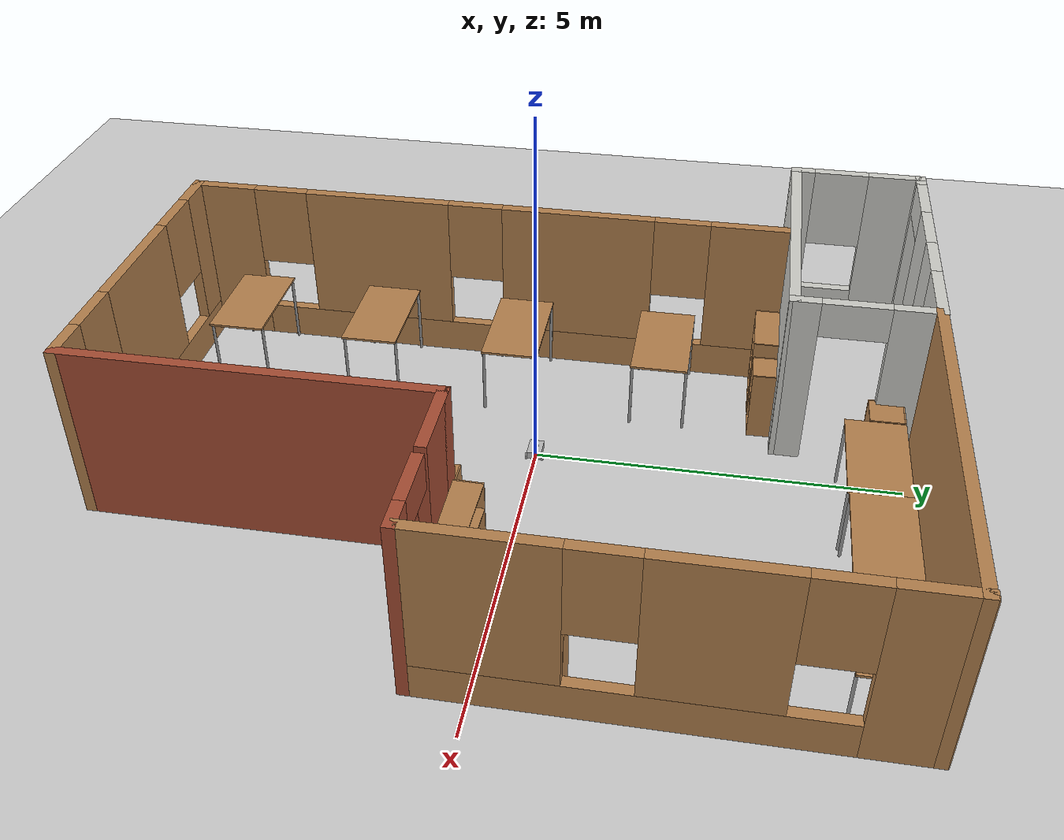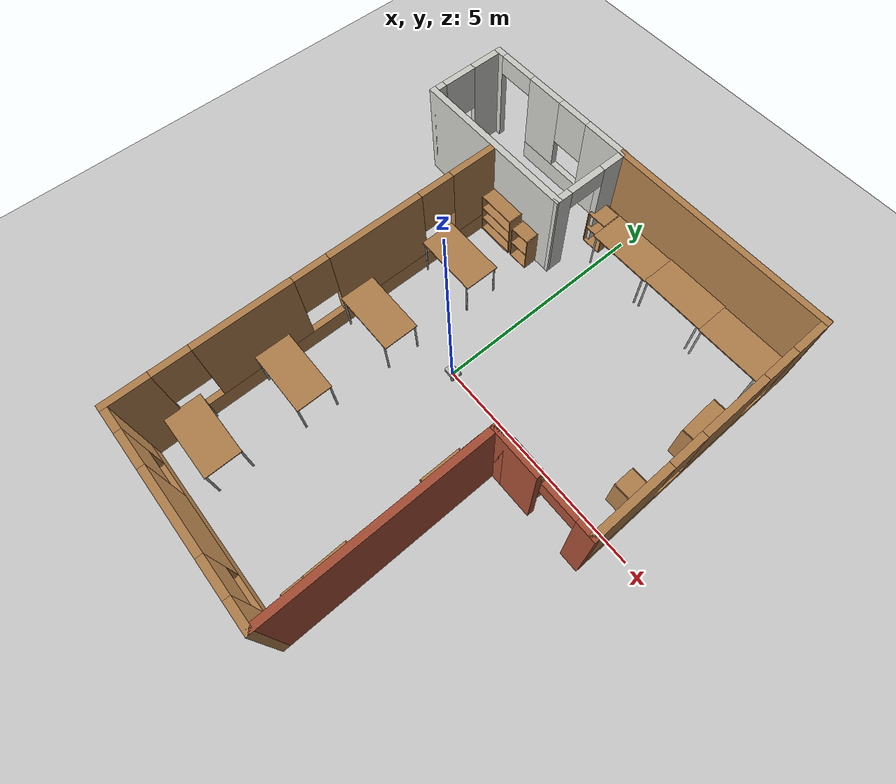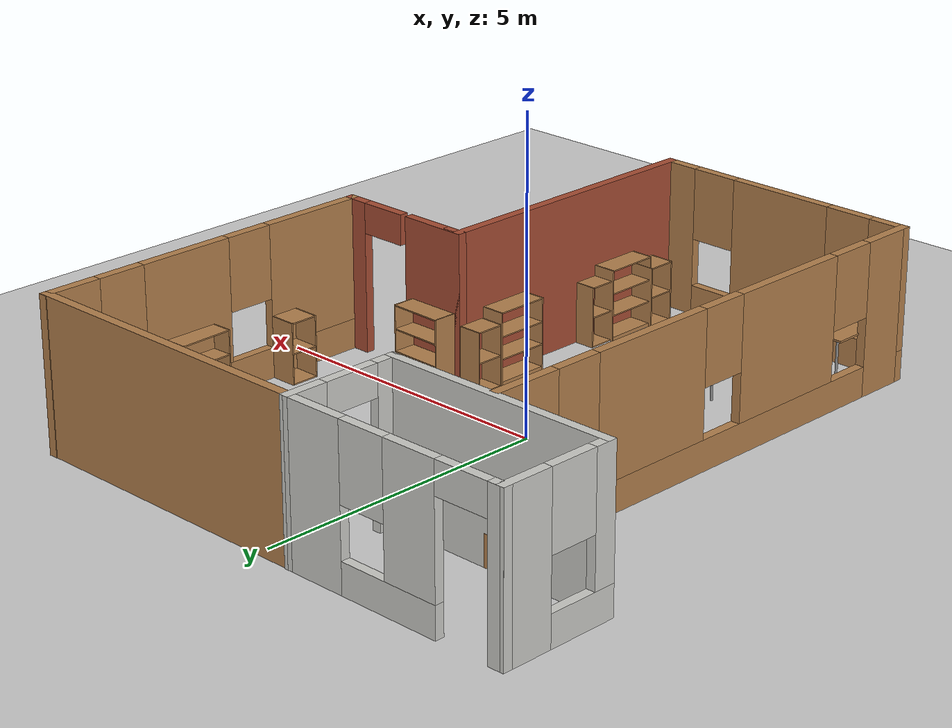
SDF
<sdf version="1.7">
 <world name="default">
  <light name="sun" type="directional">
   <pose>0 0 10 0 -0 0</pose>
   <diffuse>0.8 0.8 0.8 1</diffuse>
   <specular>0.2 0.2 0.2 1</specular>
   <attenuation>
    <range>1000</range>
    <constant>0.9</constant>
    <linear>0.01</linear>
    <quadratic>0.001</quadratic>
   </attenuation>
   <direction>-0.5 0.1 -0.9</direction>
   <spot><inner_angle>0</inner_angle><outer_angle>0</outer_angle><falloff>0</falloff></spot>
  </light>
  <model name="ground_plane">
   <static>1</static>
   <link name="link">
    <collision name="collision">
     <geometry><plane><normal>0 0 1</normal><size>100 100</size></plane></geometry>
     <surface><friction><ode><mu>100</mu><mu2>50</mu2></ode></friction></surface>
    </collision>
    <visual name="visual">
     <cast_shadows>0</cast_shadows>
     <geometry><plane><normal>0 0 1</normal><size>100 100</size></plane></geometry>
     <material>
      <script><uri>file://media/materials/scripts/gazebo.material</uri><name>Gazebo/Grey</name></script>
     </material>
    </visual>
   </link>
  </model>
  <gravity>0 0 -9.8</gravity>
  <magnetic_field>6e-06 2.3e-05 -4.2e-05</magnetic_field>
  <atmosphere type="adiabatic"/>
  <physics type="ode">
   <max_step_size>0.001</max_step_size>
   <real_time_factor>1</real_time_factor>
   <real_time_update_rate>1000</real_time_update_rate>
  </physics>
  <scene><ambient>0.4 0.4 0.4 1</ambient><background>0.7 0.7 0.7 1</background><shadows>1</shadows></scene>
  <audio><device>default</device></audio>
  <spherical_coordinates>
   <surface_model>EARTH_WGS84</surface_model>
   <latitude_deg>0</latitude_deg>
   <longitude_deg>0</longitude_deg>
   <elevation>0</elevation>
   <heading_deg>0</heading_deg>
  </spherical_coordinates>
  <model name="cafeteria_model">
   <pose>-0.0265 0.12555 0 0 -0 0</pose>
   <link name="Wall_0">
    <pose>-4.47492 4.0775 0 0 -0 -1.5708</pose>
    <visual name="Wall_0_Visual_0">
     <pose>-0.579377 0 1.25 0 -0 0</pose>
     <geometry><box><size>0.841246 0.15 2.5</size></box></geometry>
     <material>
      <script><uri>file://media/materials/scripts/gazebo.material</uri><name>Gazebo/CeilingTiled</name></script>
      <ambient>1 1 1 1</ambient>
     </material>
     <meta><layer>0</layer></meta>
    </visual>
    <collision name="Wall_0_Collision_0">
     <geometry><box><size>0.841246 0.15 2.5</size></box></geometry>
     <pose>-0.579377 0 1.25 0 -0 0</pose>
    </collision>
    <visual name="Wall_0_Visual_1">
     <pose>0.420623 0 0.25 0 -0 0</pose>
     <geometry><box><size>1.15875 0.15 0.5</size></box></geometry>
     <material>
      <script><uri>file://media/materials/scripts/gazebo.material</uri><name>Gazebo/CeilingTiled</name></script>
      <ambient>1 1 1 1</ambient>
     </material>
     <meta><layer>0</layer></meta>
    </visual>
    <collision name="Wall_0_Collision_1">
     <geometry><box><size>1.15875 0.15 0.5</size></box></geometry>
     <pose>0.420623 0 0.25 0 -0 0</pose>
    </collision>
    <visual name="Wall_0_Visual_2">
     <pose>0.820623 0 1.5 0 -0 0</pose>
     <geometry><box><size>0.358754 0.15 2</size></box></geometry>
     <material>
      <script><uri>file://media/materials/scripts/gazebo.material</uri><name>Gazebo/CeilingTiled</name></script>
      <ambient>1 1 1 1</ambient>
     </material>
     <meta><layer>0</layer></meta>
    </visual>
    <collision name="Wall_0_Collision_2">
     <geometry><box><size>0.358754 0.15 2</size></box></geometry>
     <pose>0.820623 0 1.5 0 -0 0</pose>
    </collision>
    <visual name="Wall_0_Visual_3">
     <pose>0.241246 0 1.9 0 -0 0</pose>
     <geometry><box><size>0.8 0.15 1.2</size></box></geometry>
     <material>
      <script><uri>file://media/materials/scripts/gazebo.material</uri><name>Gazebo/CeilingTiled</name></script>
      <ambient>1 1 1 1</ambient>
     </material>
     <meta><layer>0</layer></meta>
    </visual>
    <collision name="Wall_0_Collision_3">
     <geometry><box><size>0.8 0.15 1.2</size></box></geometry>
     <pose>0.241246 0 1.9 0 -0 0</pose>
    </collision>
   </link>
   <link name="Wall_1">
    <collision name="Wall_1_Collision">
     <geometry><box><size>4 0.15 2.5</size></box></geometry>
     <pose>0 0 1.25 0 -0 0</pose>
    </collision>
    <visual name="Wall_1_Visual">
     <pose>0 0 1.25 0 -0 0</pose>
     <geometry><box><size>4 0.15 2.5</size></box></geometry>
     <material>
      <script><uri>file://media/materials/scripts/gazebo.material</uri><name>Gazebo/CeilingTiled</name></script>
      <ambient>1 1 1 1</ambient>
     </material>
     <meta><layer>0</layer></meta>
    </visual>
    <pose>-2.54992 3.1525 0 0 -0 0</pose>
   </link>
   <link name="Wall_12">
    <collision name="Wall_12_Collision">
     <geometry><box><size>5 0.15 2.5</size></box></geometry>
     <pose>0 0 1.25 0 -0 0</pose>
    </collision>
    <visual name="Wall_12_Visual">
     <pose>0 0 1.25 0 -0 0</pose>
     <geometry><box><size>5 0.15 2.5</size></box></geometry>
     <material>
      <script><uri>file://media/materials/scripts/gazebo.material</uri><name>Gazebo/Bricks</name></script>
      <ambient>1 1 1 1</ambient>
     </material>
     <meta><layer>0</layer></meta>
    </visual>
    <pose>2.12508 -3.2725 0 0 -0 -1.5708</pose>
   </link>
   <link name="Wall_13">
    <pose>-0.174922 -5.6975 0 0 -0 3.14159</pose>
    <visual name="Wall_13_Visual_0">
     <pose>-2.0467 0 1.25 0 -0 0</pose>
     <geometry><box><size>0.65661 0.15 2.5</size></box></geometry>
     <material>
      <script><uri>file://media/materials/scripts/gazebo.material</uri><name>Gazebo/Wood</name></script>
      <ambient>1 1 1 1</ambient>
     </material>
     <meta><layer>0</layer></meta>
    </visual>
    <collision name="Wall_13_Collision_0">
     <geometry><box><size>0.65661 0.15 2.5</size></box></geometry>
     <pose>-2.0467 0 1.25 0 -0 0</pose>
    </collision>
    <visual name="Wall_13_Visual_1">
     <pose>0.328305 0 0.25 0 -0 0</pose>
     <geometry><box><size>4.09339 0.15 0.5</size></box></geometry>
     <material>
      <script><uri>file://media/materials/scripts/gazebo.material</uri><name>Gazebo/Wood</name></script>
      <ambient>1 1 1 1</ambient>
     </material>
     <meta><layer>0</layer></meta>
    </visual>
    <collision name="Wall_13_Collision_1">
     <geometry><box><size>4.09339 0.15 0.5</size></box></geometry>
     <pose>0.328305 0 0.25 0 -0 0</pose>
    </collision>
    <visual name="Wall_13_Visual_2">
     <pose>0.00446 0 1.5 0 -0 0</pose>
     <geometry><box><size>1.8457 0.15 2</size></box></geometry>
     <material>
      <script><uri>file://media/materials/scripts/gazebo.material</uri><name>Gazebo/Wood</name></script>
      <ambient>1 1 1 1</ambient>
     </material>
     <meta><layer>0</layer></meta>
    </visual>
    <collision name="Wall_13_Collision_2">
     <geometry><box><size>1.8457 0.15 2</size></box></geometry>
     <pose>0.00446 0 1.5 0 -0 0</pose>
    </collision>
    <visual name="Wall_13_Visual_3">
     <pose>2.05115 0 1.5 0 -0 0</pose>
     <geometry><box><size>0.647691 0.15 2</size></box></geometry>
     <material>
      <script><uri>file://media/materials/scripts/gazebo.material</uri><name>Gazebo/Wood</name></script>
      <ambient>1 1 1 1</ambient>
     </material>
     <meta><layer>0</layer></meta>
    </visual>
    <collision name="Wall_13_Collision_3">
     <geometry><box><size>0.647691 0.15 2</size></box></geometry>
     <pose>2.05115 0 1.5 0 -0 0</pose>
    </collision>
    <visual name="Wall_13_Visual_4">
     <pose>-1.31839 0 1.9 0 -0 0</pose>
     <geometry><box><size>0.8 0.15 1.2</size></box></geometry>
     <material>
      <script><uri>file://media/materials/scripts/gazebo.material</uri><name>Gazebo/Wood</name></script>
      <ambient>1 1 1 1</ambient>
     </material>
     <meta><layer>0</layer></meta>
    </visual>
    <collision name="Wall_13_Collision_4">
     <geometry><box><size>0.8 0.15 1.2</size></box></geometry>
     <pose>-1.31839 0 1.9 0 -0 0</pose>
    </collision>
    <visual name="Wall_13_Visual_5">
     <pose>1.32731 0 1.9 0 -0 0</pose>
     <geometry><box><size>0.8 0.15 1.2</size></box></geometry>
     <material>
      <script><uri>file://media/materials/scripts/gazebo.material</uri><name>Gazebo/Wood</name></script>
      <ambient>1 1 1 1</ambient>
     </material>
     <meta><layer>0</layer></meta>
    </visual>
    <collision name="Wall_13_Collision_5">
     <geometry><box><size>0.8 0.15 1.2</size></box></geometry>
     <pose>1.32731 0 1.9 0 -0 0</pose>
    </collision>
   </link>
   <link name="Wall_14">
    <pose>-2.47492 -1.2725 0 0 -0 1.5708</pose>
    <visual name="Wall_14_Visual_0">
     <pose>-4.01175 0 1.25 0 -0 0</pose>
     <geometry><box><size>0.976501 0.15 2.5</size></box></geometry>
     <material>
      <script><uri>file://media/materials/scripts/gazebo.material</uri><name>Gazebo/Wood</name></script>
      <ambient>1 1 1 1</ambient>
     </material>
     <meta><layer>0</layer></meta>
    </visual>
    <collision name="Wall_14_Collision_0">
     <geometry><box><size>0.976501 0.15 2.5</size></box></geometry>
     <pose>-4.01175 0 1.25 0 -0 0</pose>
    </collision>
    <visual name="Wall_14_Visual_1">
     <pose>0.488251 0 0.25 0 -0 0</pose>
     <geometry><box><size>8.0235 0.15 0.5</size></box></geometry>
     <material>
      <script><uri>file://media/materials/scripts/gazebo.material</uri><name>Gazebo/Wood</name></script>
      <ambient>1 1 1 1</ambient>
     </material>
     <meta><layer>0</layer></meta>
    </visual>
    <collision name="Wall_14_Collision_1">
     <geometry><box><size>8.0235 0.15 0.5</size></box></geometry>
     <pose>0.488251 0 0.25 0 -0 0</pose>
    </collision>
    <visual name="Wall_14_Visual_2">
     <pose>-1.64683 0 1.5 0 -0 0</pose>
     <geometry><box><size>2.15334 0.15 2</size></box></geometry>
     <material>
      <script><uri>file://media/materials/scripts/gazebo.material</uri><name>Gazebo/Wood</name></script>
      <ambient>1 1 1 1</ambient>
     </material>
     <meta><layer>0</layer></meta>
    </visual>
    <collision name="Wall_14_Collision_2">
     <geometry><box><size>2.15334 0.15 2</size></box></geometry>
     <pose>-1.64683 0 1.5 0 -0 0</pose>
    </collision>
    <visual name="Wall_14_Visual_3">
     <pose>1.33727 0 1.5 0 -0 0</pose>
     <geometry><box><size>2.21487 0.15 2</size></box></geometry>
     <material>
      <script><uri>file://media/materials/scripts/gazebo.material</uri><name>Gazebo/Wood</name></script>
      <ambient>1 1 1 1</ambient>
     </material>
     <meta><layer>0</layer></meta>
    </visual>
    <collision name="Wall_14_Collision_3">
     <geometry><box><size>2.21487 0.15 2</size></box></geometry>
     <pose>1.33727 0 1.5 0 -0 0</pose>
    </collision>
    <visual name="Wall_14_Visual_4">
     <pose>3.87235 0 1.5 0 -0 0</pose>
     <geometry><box><size>1.2553 0.15 2</size></box></geometry>
     <material>
      <script><uri>file://media/materials/scripts/gazebo.material</uri><name>Gazebo/Wood</name></script>
      <ambient>1 1 1 1</ambient>
     </material>
     <meta><layer>0</layer></meta>
    </visual>
    <collision name="Wall_14_Collision_4">
     <geometry><box><size>1.2553 0.15 2</size></box></geometry>
     <pose>3.87235 0 1.5 0 -0 0</pose>
    </collision>
    <visual name="Wall_14_Visual_5">
     <pose>-3.1235 0 1.9 0 -0 0</pose>
     <geometry><box><size>0.8 0.15 1.2</size></box></geometry>
     <material>
      <script><uri>file://media/materials/scripts/gazebo.material</uri><name>Gazebo/Wood</name></script>
      <ambient>1 1 1 1</ambient>
     </material>
     <meta><layer>0</layer></meta>
    </visual>
    <collision name="Wall_14_Collision_5">
     <geometry><box><size>0.8 0.15 1.2</size></box></geometry>
     <pose>-3.1235 0 1.9 0 -0 0</pose>
    </collision>
    <visual name="Wall_14_Visual_6">
     <pose>-0.170161 0 1.9 0 -0 0</pose>
     <geometry><box><size>0.8 0.15 1.2</size></box></geometry>
     <material>
      <script><uri>file://media/materials/scripts/gazebo.material</uri><name>Gazebo/Wood</name></script>
      <ambient>1 1 1 1</ambient>
     </material>
     <meta><layer>0</layer></meta>
    </visual>
    <collision name="Wall_14_Collision_6">
     <geometry><box><size>0.8 0.15 1.2</size></box></geometry>
     <pose>-0.170161 0 1.9 0 -0 0</pose>
    </collision>
    <visual name="Wall_14_Visual_7">
     <pose>2.8447 0 1.9 0 -0 0</pose>
     <geometry><box><size>0.8 0.15 1.2</size></box></geometry>
     <material>
      <script><uri>file://media/materials/scripts/gazebo.material</uri><name>Gazebo/Wood</name></script>
      <ambient>1 1 1 1</ambient>
     </material>
     <meta><layer>0</layer></meta>
    </visual>
    <collision name="Wall_14_Collision_7">
     <geometry><box><size>0.8 0.15 1.2</size></box></geometry>
     <pose>2.8447 0 1.9 0 -0 0</pose>
    </collision>
   </link>
   <link name="Wall_2">
    <pose>-0.624876 4.07892 0 0 -0 1.57075</pose>
    <visual name="Wall_2_Visual_0">
     <pose>-0.793545 0 1.25 0 -0 0</pose>
     <geometry><box><size>0.415751 0.15 2.5</size></box></geometry>
     <material>
      <script><uri>file://media/materials/scripts/gazebo.material</uri><name>Gazebo/CeilingTiled</name></script>
      <ambient>1 1 1 1</ambient>
     </material>
     <meta><layer>0</layer></meta>
    </visual>
    <collision name="Wall_2_Collision_0">
     <geometry><box><size>0.415751 0.15 2.5</size></box></geometry>
     <pose>-0.793545 0 1.25 0 -0 0</pose>
    </collision>
    <visual name="Wall_2_Visual_1">
     <pose>0.657876 0 1.25 0 -0 0</pose>
     <geometry><box><size>0.687089 0.15 2.5</size></box></geometry>
     <material>
      <script><uri>file://media/materials/scripts/gazebo.material</uri><name>Gazebo/CeilingTiled</name></script>
      <ambient>1 1 1 1</ambient>
     </material>
     <meta><layer>0</layer></meta>
    </visual>
    <collision name="Wall_2_Collision_1">
     <geometry><box><size>0.687089 0.15 2.5</size></box></geometry>
     <pose>0.657876 0 1.25 0 -0 0</pose>
    </collision>
    <visual name="Wall_2_Visual_2">
     <pose>-0.135669 0 2.25 0 -0 0</pose>
     <geometry><box><size>0.9 0.15 0.5</size></box></geometry>
     <material>
      <script><uri>file://media/materials/scripts/gazebo.material</uri><name>Gazebo/CeilingTiled</name></script>
      <ambient>1 1 1 1</ambient>
     </material>
     <meta><layer>0</layer></meta>
    </visual>
    <collision name="Wall_2_Collision_2">
     <geometry><box><size>0.9 0.15 0.5</size></box></geometry>
     <pose>-0.135669 0 2.25 0 -0 0</pose>
    </collision>
   </link>
   <link name="Wall_3">
    <pose>-2.54988 5.00392 0 0 -0 -3.14086</pose>
    <visual name="Wall_3_Visual_0">
     <pose>-1.44635 0 1.25 0 -0 0</pose>
     <geometry><box><size>1.10778 0.15 2.5</size></box></geometry>
     <material>
      <script><uri>file://media/materials/scripts/gazebo.material</uri><name>Gazebo/CeilingTiled</name></script>
      <ambient>1 1 1 1</ambient>
     </material>
     <meta><layer>0</layer></meta>
    </visual>
    <collision name="Wall_3_Collision_0">
     <geometry><box><size>1.10778 0.15 2.5</size></box></geometry>
     <pose>-1.44635 0 1.25 0 -0 0</pose>
    </collision>
    <visual name="Wall_3_Visual_1">
     <pose>1.86162 0 1.25 0 -0 0</pose>
     <geometry><box><size>0.27724 0.15 2.5</size></box></geometry>
     <material>
      <script><uri>file://media/materials/scripts/gazebo.material</uri><name>Gazebo/CeilingTiled</name></script>
      <ambient>1 1 1 1</ambient>
     </material>
     <meta><layer>0</layer></meta>
    </visual>
    <collision name="Wall_3_Collision_1">
     <geometry><box><size>0.27724 0.15 2.5</size></box></geometry>
     <pose>1.86162 0 1.25 0 -0 0</pose>
    </collision>
    <visual name="Wall_3_Visual_2">
     <pose>-0.034732 0 0.25 0 -0 0</pose>
     <geometry><box><size>1.71546 0.15 0.5</size></box></geometry>
     <material>
      <script><uri>file://media/materials/scripts/gazebo.material</uri><name>Gazebo/CeilingTiled</name></script>
      <ambient>1 1 1 1</ambient>
     </material>
     <meta><layer>0</layer></meta>
    </visual>
    <collision name="Wall_3_Collision_2">
     <geometry><box><size>1.71546 0.15 0.5</size></box></geometry>
     <pose>-0.034732 0 0.25 0 -0 0</pose>
    </collision>
    <visual name="Wall_3_Visual_3">
     <pose>0.365268 0 1.5 0 -0 0</pose>
     <geometry><box><size>0.915463 0.15 2</size></box></geometry>
     <material>
      <script><uri>file://media/materials/scripts/gazebo.material</uri><name>Gazebo/CeilingTiled</name></script>
      <ambient>1 1 1 1</ambient>
     </material>
     <meta><layer>0</layer></meta>
    </visual>
    <collision name="Wall_3_Collision_3">
     <geometry><box><size>0.915463 0.15 2</size></box></geometry>
     <pose>0.365268 0 1.5 0 -0 0</pose>
    </collision>
    <visual name="Wall_3_Visual_4">
     <pose>-0.492464 0 1.9 0 -0 0</pose>
     <geometry><box><size>0.8 0.15 1.2</size></box></geometry>
     <material>
      <script><uri>file://media/materials/scripts/gazebo.material</uri><name>Gazebo/CeilingTiled</name></script>
      <ambient>1 1 1 1</ambient>
     </material>
     <meta><layer>0</layer></meta>
    </visual>
    <collision name="Wall_3_Collision_4">
     <geometry><box><size>0.8 0.15 1.2</size></box></geometry>
     <pose>-0.492464 0 1.9 0 -0 0</pose>
    </collision>
    <visual name="Wall_3_Visual_5">
     <pose>1.273 0 2.25 0 -0 0</pose>
     <geometry><box><size>0.9 0.15 0.5</size></box></geometry>
     <material>
      <script><uri>file://media/materials/scripts/gazebo.material</uri><name>Gazebo/CeilingTiled</name></script>
      <ambient>1 1 1 1</ambient>
     </material>
     <meta><layer>0</layer></meta>
    </visual>
    <collision name="Wall_3_Collision_5">
     <geometry><box><size>0.9 0.15 0.5</size></box></geometry>
     <pose>1.273 0 2.25 0 -0 0</pose>
    </collision>
   </link>
   <link name="Wall_5">
    <collision name="Wall_5_Collision">
     <geometry><box><size>5.25 0.15 2.5</size></box></geometry>
     <pose>0 0 1.25 0 -0 0</pose>
    </collision>
    <visual name="Wall_5_Visual">
     <pose>0 0 1.25 0 -0 0</pose>
     <geometry><box><size>5.25 0.15 2.5</size></box></geometry>
     <material>
      <script><uri>file://media/materials/scripts/gazebo.material</uri><name>Gazebo/Wood</name></script>
      <ambient>1 1 1 1</ambient>
     </material>
     <meta><layer>0</layer></meta>
    </visual>
    <pose>1.92517 4.99384 0 0 -0 0</pose>
   </link>
   <link name="Wall_8">
    <pose>4.47512 2.07892 0 0 -0 -1.57081</pose>
    <visual name="Wall_8_Visual_0">
     <pose>-2.52409 0 1.25 0 -0 0</pose>
     <geometry><box><size>0.95466 0.15 2.5</size></box></geometry>
     <material>
      <script><uri>file://media/materials/scripts/gazebo.material</uri><name>Gazebo/Wood</name></script>
      <ambient>1 1 1 1</ambient>
     </material>
     <meta><layer>0</layer></meta>
    </visual>
    <collision name="Wall_8_Collision_0">
     <geometry><box><size>0.95466 0.15 2.5</size></box></geometry>
     <pose>-2.52409 0 1.25 0 -0 0</pose>
    </collision>
    <visual name="Wall_8_Visual_1">
     <pose>0.47733 0 0.25 0 -0 0</pose>
     <geometry><box><size>5.04818 0.15 0.5</size></box></geometry>
     <material>
      <script><uri>file://media/materials/scripts/gazebo.material</uri><name>Gazebo/Wood</name></script>
      <ambient>1 1 1 1</ambient>
     </material>
     <meta><layer>0</layer></meta>
    </visual>
    <collision name="Wall_8_Collision_1">
     <geometry><box><size>5.04818 0.15 0.5</size></box></geometry>
     <pose>0.47733 0 0.25 0 -0 0</pose>
    </collision>
    <visual name="Wall_8_Visual_2">
     <pose>-0.446966 0 1.5 0 -0 0</pose>
     <geometry><box><size>1.59959 0.15 2</size></box></geometry>
     <material>
      <script><uri>file://media/materials/scripts/gazebo.material</uri><name>Gazebo/Wood</name></script>
      <ambient>1 1 1 1</ambient>
     </material>
     <meta><layer>0</layer></meta>
    </visual>
    <collision name="Wall_8_Collision_2">
     <geometry><box><size>1.59959 0.15 2</size></box></geometry>
     <pose>-0.446966 0 1.5 0 -0 0</pose>
    </collision>
    <visual name="Wall_8_Visual_3">
     <pose>2.07712 0 1.5 0 -0 0</pose>
     <geometry><box><size>1.84859 0.15 2</size></box></geometry>
     <material>
      <script><uri>file://media/materials/scripts/gazebo.material</uri><name>Gazebo/Wood</name></script>
      <ambient>1 1 1 1</ambient>
     </material>
     <meta><layer>0</layer></meta>
    </visual>
    <collision name="Wall_8_Collision_3">
     <geometry><box><size>1.84859 0.15 2</size></box></geometry>
     <pose>2.07712 0 1.5 0 -0 0</pose>
    </collision>
    <visual name="Wall_8_Visual_4">
     <pose>-1.64676 0 1.9 0 -0 0</pose>
     <geometry><box><size>0.8 0.15 1.2</size></box></geometry>
     <material>
      <script><uri>file://media/materials/scripts/gazebo.material</uri><name>Gazebo/Wood</name></script>
      <ambient>1 1 1 1</ambient>
     </material>
     <meta><layer>0</layer></meta>
    </visual>
    <collision name="Wall_8_Collision_4">
     <geometry><box><size>0.8 0.15 1.2</size></box></geometry>
     <pose>-1.64676 0 1.9 0 -0 0</pose>
    </collision>
    <visual name="Wall_8_Visual_5">
     <pose>0.752828 0 1.9 0 -0 0</pose>
     <geometry><box><size>0.8 0.15 1.2</size></box></geometry>
     <material>
      <script><uri>file://media/materials/scripts/gazebo.material</uri><name>Gazebo/Wood</name></script>
      <ambient>1 1 1 1</ambient>
     </material>
     <meta><layer>0</layer></meta>
    </visual>
    <collision name="Wall_8_Collision_5">
     <geometry><box><size>0.8 0.15 1.2</size></box></geometry>
     <pose>0.752828 0 1.9 0 -0 0</pose>
    </collision>
   </link>
   <link name="Wall_9">
    <pose>3.30008 -0.8475 0 0 -0 3.14159</pose>
    <visual name="Wall_9_Visual_0">
     <pose>-1.03302 0 1.25 0 -0 0</pose>
     <geometry><box><size>0.433967 0.15 2.5</size></box></geometry>
     <material>
      <script><uri>file://media/materials/scripts/gazebo.material</uri><name>Gazebo/Bricks</name></script>
      <ambient>1 1 1 1</ambient>
     </material>
     <meta><layer>0</layer></meta>
    </visual>
    <collision name="Wall_9_Collision_0">
     <geometry><box><size>0.433967 0.15 2.5</size></box></geometry>
     <pose>-1.03302 0 1.25 0 -0 0</pose>
    </collision>
    <visual name="Wall_9_Visual_1">
     <pose>0.666984 0 1.25 0 -0 0</pose>
     <geometry><box><size>1.16603 0.15 2.5</size></box></geometry>
     <material>
      <script><uri>file://media/materials/scripts/gazebo.material</uri><name>Gazebo/Bricks</name></script>
      <ambient>1 1 1 1</ambient>
     </material>
     <meta><layer>0</layer></meta>
    </visual>
    <collision name="Wall_9_Collision_1">
     <geometry><box><size>1.16603 0.15 2.5</size></box></geometry>
     <pose>0.666984 0 1.25 0 -0 0</pose>
    </collision>
    <visual name="Wall_9_Visual_2">
     <pose>1.06692 0 1.25 0 -0 0</pose>
     <geometry><box><size>0.36617 0.15 2.5</size></box></geometry>
     <material>
      <script><uri>file://media/materials/scripts/gazebo.material</uri><name>Gazebo/Bricks</name></script>
      <ambient>1 1 1 1</ambient>
     </material>
     <meta><layer>0</layer></meta>
    </visual>
    <collision name="Wall_9_Collision_2">
     <geometry><box><size>0.36617 0.15 2.5</size></box></geometry>
     <pose>1.06692 0 1.25 0 -0 0</pose>
    </collision>
    <visual name="Wall_9_Visual_3">
     <pose>-0.416101 0 2.25 0 -0 0</pose>
     <geometry><box><size>0.799862 0.15 0.5</size></box></geometry>
     <material>
      <script><uri>file://media/materials/scripts/gazebo.material</uri><name>Gazebo/Bricks</name></script>
      <ambient>1 1 1 1</ambient>
     </material>
     <meta><layer>0</layer></meta>
    </visual>
    <collision name="Wall_9_Collision_3">
     <geometry><box><size>0.799862 0.15 0.5</size></box></geometry>
     <pose>-0.416101 0 2.25 0 -0 0</pose>
    </collision>
   </link>
   <static>1</static>
  </model>
  <model name="bookshelf">
   <static>1</static>
   <link name="link">
    <inertial><mass>1</mass></inertial>
    <collision name="back">
     <pose>0 0.005 0.6 0 -0 0</pose>
     <geometry><box><size>0.9 0.01 1.2</size></box></geometry>
    </collision>
    <visual name="visual1">
     <pose>0 0.005 0.6 0 -0 0</pose>
     <geometry><box><size>0.9 0.01 1.2</size></box></geometry>
     <material>
      <script><uri>file://media/materials/scripts/gazebo.material</uri><name>Gazebo/Wood</name></script>
     </material>
    </visual>
    <collision name="left_side">
     <pose>0.45 -0.195 0.6 0 -0 0</pose>
     <geometry><box><size>0.02 0.4 1.2</size></box></geometry>
    </collision>
    <visual name="visual2">
     <pose>0.45 -0.195 0.6 0 -0 0</pose>
     <geometry><box><size>0.02 0.4 1.2</size></box></geometry>
     <material>
      <script><uri>file://media/materials/scripts/gazebo.material</uri><name>Gazebo/Wood</name></script>
     </material>
    </visual>
    <collision name="right_side">
     <pose>-0.45 -0.195 0.6 0 -0 0</pose>
     <geometry><box><size>0.02 0.4 1.2</size></box></geometry>
    </collision>
    <visual name="visual3">
     <pose>-0.45 -0.195 0.6 0 -0 0</pose>
     <geometry><box><size>0.02 0.4 1.2</size></box></geometry>
     <material>
      <script><uri>file://media/materials/scripts/gazebo.material</uri><name>Gazebo/Wood</name></script>
     </material>
    </visual>
    <collision name="bottom">
     <pose>0 -0.195 0.03 0 -0 0</pose>
     <geometry><box><size>0.88 0.4 0.06</size></box></geometry>
    </collision>
    <visual name="visual4">
     <pose>0 -0.195 0.03 0 -0 0</pose>
     <geometry><box><size>0.88 0.4 0.06</size></box></geometry>
     <material>
      <script><uri>file://media/materials/scripts/gazebo.material</uri><name>Gazebo/Wood</name></script>
     </material>
    </visual>
    <collision name="top">
     <pose>0 -0.195 1.19 0 -0 0</pose>
     <geometry><box><size>0.88 0.4 0.02</size></box></geometry>
    </collision>
    <visual name="visual5">
     <pose>0 -0.195 1.19 0 -0 0</pose>
     <geometry><box><size>0.88 0.4 0.02</size></box></geometry>
     <material>
      <script><uri>file://media/materials/scripts/gazebo.material</uri><name>Gazebo/Wood</name></script>
     </material>
    </visual>
    <collision name="low_shelf">
     <pose>0 -0.195 0.43 0 -0 0</pose>
     <geometry><box><size>0.88 0.4 0.02</size></box></geometry>
    </collision>
    <visual name="visual6">
     <pose>0 -0.195 0.43 0 -0 0</pose>
     <geometry><box><size>0.88 0.4 0.02</size></box></geometry>
     <material>
      <script><uri>file://media/materials/scripts/gazebo.material</uri><name>Gazebo/Wood</name></script>
     </material>
    </visual>
    <collision name="high_shelf">
     <pose>0 -0.195 0.8 0 -0 0</pose>
     <geometry><box><size>0.88 0.4 0.02</size></box></geometry>
    </collision>
    <visual name="visual7">
     <pose>0 -0.195 0.8 0 -0 0</pose>
     <geometry><box><size>0.88 0.4 0.02</size></box></geometry>
     <material>
      <script><uri>file://media/materials/scripts/gazebo.material</uri><name>Gazebo/Wood</name></script>
     </material>
    </visual>
   </link>
   <pose>-1.96041 3.25452 0 0 -0 0</pose>
  </model>
  <model name="cabinet">
   <static>1</static>
   <link name="cabinet_bottom_plate">
    <inertial>
     <pose>0 0 -1 0 -0 0</pose>
     <inertia><ixx>2.05</ixx><ixy>0</ixy><ixz>0</ixz><iyy>2.05</iyy><iyz>0</iyz><izz>2.05</izz></inertia>
     <mass>25</mass>
    </inertial>
    <collision name="cabinet_bottom_plate_geom">
     <pose>0 0 0.01 0 -0 0</pose>
     <geometry><box><size>0.45 0.45 0.02</size></box></geometry>
    </collision>
    <visual name="cabinet_bottom_plate_geom_visual">
     <pose>0 0 0.01 0 -0 0</pose>
     <geometry><box><size>0.45 0.45 0.02</size></box></geometry>
     <material>
      <script><uri>file://media/materials/scripts/gazebo.material</uri><name>Gazebo/Wood</name></script>
     </material>
    </visual>
    <collision name="cabinet_bottom_plate_geom_cabinet_back_plate">
     <pose>0.235 0 0.51 0 -0 0</pose>
     <geometry><box><size>0.02 0.45 1.02</size></box></geometry>
    </collision>
    <visual name="cabinet_bottom_plate_geom_cabinet_back_plate_visual">
     <pose>0.235 0 0.51 0 -0 0</pose>
     <geometry><box><size>0.02 0.45 1.02</size></box></geometry>
     <material>
      <script><uri>file://media/materials/scripts/gazebo.material</uri><name>Gazebo/Wood</name></script>
     </material>
    </visual>
    <collision name="cabinet_bottom_plate_geom_cabinet_left_plate">
     <pose>0 0.235 0.51 0 -0 0</pose>
     <geometry><box><size>0.45 0.02 1.02</size></box></geometry>
    </collision>
    <visual name="cabinet_bottom_plate_geom_cabinet_left_plate_visual">
     <pose>0 0.235 0.51 0 -0 0</pose>
     <geometry><box><size>0.45 0.02 1.02</size></box></geometry>
     <material>
      <script><uri>file://media/materials/scripts/gazebo.material</uri><name>Gazebo/Wood</name></script>
     </material>
    </visual>
    <collision name="cabinet_bottom_plate_geom_cabinet_middle_plate">
     <pose>0 0 0.51 0 -0 0</pose>
     <geometry><box><size>0.45 0.45 0.02</size></box></geometry>
    </collision>
    <visual name="cabinet_bottom_plate_geom_cabinet_middle_plate_visual">
     <pose>0 0 0.51 0 -0 0</pose>
     <geometry><box><size>0.45 0.45 0.02</size></box></geometry>
     <material>
      <script><uri>file://media/materials/scripts/gazebo.material</uri><name>Gazebo/Wood</name></script>
     </material>
    </visual>
    <collision name="cabinet_bottom_plate_geom_cabinet_right_plate">
     <pose>0 -0.235 0.51 0 -0 0</pose>
     <geometry><box><size>0.45 0.02 1.02</size></box></geometry>
    </collision>
    <visual name="cabinet_bottom_plate_geom_cabinet_right_plate_visual">
     <pose>0 -0.235 0.51 0 -0 0</pose>
     <geometry><box><size>0.45 0.02 1.02</size></box></geometry>
     <material>
      <script><uri>file://media/materials/scripts/gazebo.material</uri><name>Gazebo/Wood</name></script>
     </material>
    </visual>
    <collision name="cabinet_bottom_plate_geom_cabinet_top_plate">
     <pose>0 0 1.01 0 -0 0</pose>
     <geometry><box><size>0.45 0.45 0.02</size></box></geometry>
    </collision>
    <visual name="cabinet_bottom_plate_geom_cabinet_top_plate_visual">
     <pose>0 0 1.01 0 -0 0</pose>
     <geometry><box><size>0.45 0.45 0.02</size></box></geometry>
     <material>
      <script><uri>file://media/materials/scripts/gazebo.material</uri><name>Gazebo/Wood</name></script>
     </material>
    </visual>
   </link>
   <pose>1.85545 -0.907747 0 0 -0 0</pose>
  </model>
  <model name="table">
   <static>1</static>
   <link name="link">
    <collision name="surface">
     <pose>0 0 1 0 -0 0</pose>
     <geometry><box><size>1.5 0.8 0.03</size></box></geometry>
     <surface><friction><ode><mu>0.6</mu><mu2>0.6</mu2></ode></friction></surface>
    </collision>
    <visual name="visual1">
     <pose>0 0 1 0 -0 0</pose>
     <geometry><box><size>1.5 0.8 0.03</size></box></geometry>
     <material>
      <script><uri>file://media/materials/scripts/gazebo.material</uri><name>Gazebo/Wood</name></script>
     </material>
    </visual>
    <collision name="front_left_leg">
     <pose>0.68 0.38 0.5 0 -0 0</pose>
     <geometry><cylinder><radius>0.02</radius><length>1</length></cylinder></geometry>
    </collision>
    <visual name="front_left_leg">
     <pose>0.68 0.38 0.5 0 -0 0</pose>
     <geometry><cylinder><radius>0.02</radius><length>1</length></cylinder></geometry>
     <material>
      <script><uri>file://media/materials/scripts/gazebo.material</uri><name>Gazebo/Grey</name></script>
     </material>
    </visual>
    <collision name="front_right_leg">
     <pose>0.68 -0.38 0.5 0 -0 0</pose>
     <geometry><cylinder><radius>0.02</radius><length>1</length></cylinder></geometry>
    </collision>
    <visual name="front_right_leg">
     <pose>0.68 -0.38 0.5 0 -0 0</pose>
     <geometry><cylinder><radius>0.02</radius><length>1</length></cylinder></geometry>
     <material>
      <script><uri>file://media/materials/scripts/gazebo.material</uri><name>Gazebo/Grey</name></script>
     </material>
    </visual>
    <collision name="back_right_leg">
     <pose>-0.68 -0.38 0.5 0 -0 0</pose>
     <geometry><cylinder><radius>0.02</radius><length>1</length></cylinder></geometry>
    </collision>
    <visual name="back_right_leg">
     <pose>-0.68 -0.38 0.5 0 -0 0</pose>
     <geometry><cylinder><radius>0.02</radius><length>1</length></cylinder></geometry>
     <material>
      <script><uri>file://media/materials/scripts/gazebo.material</uri><name>Gazebo/Grey</name></script>
     </material>
    </visual>
    <collision name="back_left_leg">
     <pose>-0.68 0.38 0.5 0 -0 0</pose>
     <geometry><cylinder><radius>0.02</radius><length>1</length></cylinder></geometry>
    </collision>
    <visual name="back_left_leg">
     <pose>-0.68 0.38 0.5 0 -0 0</pose>
     <geometry><cylinder><radius>0.02</radius><length>1</length></cylinder></geometry>
     <material>
      <script><uri>file://media/materials/scripts/gazebo.material</uri><name>Gazebo/Grey</name></script>
     </material>
    </visual>
   </link>
   <pose>-1.70541 -4.6233 0 0 -0 0</pose>
  </model>
  <model name="table_clone">
   <static>1</static>
   <link name="link">
    <collision name="surface">
     <pose>0 0 1 0 -0 0</pose>
     <geometry><box><size>1.5 0.8 0.03</size></box></geometry>
     <surface><friction><ode><mu>0.6</mu><mu2>0.6</mu2></ode></friction></surface>
    </collision>
    <visual name="visual1">
     <pose>0 0 1 0 -0 0</pose>
     <geometry><box><size>1.5 0.8 0.03</size></box></geometry>
     <material>
      <script><uri>file://media/materials/scripts/gazebo.material</uri><name>Gazebo/Wood</name></script>
     </material>
    </visual>
    <collision name="front_left_leg">
     <pose>0.68 0.38 0.5 0 -0 0</pose>
     <geometry><cylinder><radius>0.02</radius><length>1</length></cylinder></geometry>
    </collision>
    <visual name="front_left_leg">
     <pose>0.68 0.38 0.5 0 -0 0</pose>
     <geometry><cylinder><radius>0.02</radius><length>1</length></cylinder></geometry>
     <material>
      <script><uri>file://media/materials/scripts/gazebo.material</uri><name>Gazebo/Grey</name></script>
     </material>
    </visual>
    <collision name="front_right_leg">
     <pose>0.68 -0.38 0.5 0 -0 0</pose>
     <geometry><cylinder><radius>0.02</radius><length>1</length></cylinder></geometry>
    </collision>
    <visual name="front_right_leg">
     <pose>0.68 -0.38 0.5 0 -0 0</pose>
     <geometry><cylinder><radius>0.02</radius><length>1</length></cylinder></geometry>
     <material>
      <script><uri>file://media/materials/scripts/gazebo.material</uri><name>Gazebo/Grey</name></script>
     </material>
    </visual>
    <collision name="back_right_leg">
     <pose>-0.68 -0.38 0.5 0 -0 0</pose>
     <geometry><cylinder><radius>0.02</radius><length>1</length></cylinder></geometry>
    </collision>
    <visual name="back_right_leg">
     <pose>-0.68 -0.38 0.5 0 -0 0</pose>
     <geometry><cylinder><radius>0.02</radius><length>1</length></cylinder></geometry>
     <material>
      <script><uri>file://media/materials/scripts/gazebo.material</uri><name>Gazebo/Grey</name></script>
     </material>
    </visual>
    <collision name="back_left_leg">
     <pose>-0.68 0.38 0.5 0 -0 0</pose>
     <geometry><cylinder><radius>0.02</radius><length>1</length></cylinder></geometry>
    </collision>
    <visual name="back_left_leg">
     <pose>-0.68 0.38 0.5 0 -0 0</pose>
     <geometry><cylinder><radius>0.02</radius><length>1</length></cylinder></geometry>
     <material>
      <script><uri>file://media/materials/scripts/gazebo.material</uri><name>Gazebo/Grey</name></script>
     </material>
    </visual>
   </link>
   <pose>-1.69612 -2.61119 0 0 -0 0</pose>
  </model>
  <model name="table_clone_0">
   <static>1</static>
   <link name="link">
    <collision name="surface">
     <pose>0 0 1 0 -0 0</pose>
     <geometry><box><size>1.5 0.8 0.03</size></box></geometry>
     <surface><friction><ode><mu>0.6</mu><mu2>0.6</mu2></ode></friction></surface>
    </collision>
    <visual name="visual1">
     <pose>0 0 1 0 -0 0</pose>
     <geometry><box><size>1.5 0.8 0.03</size></box></geometry>
     <material>
      <script><uri>file://media/materials/scripts/gazebo.material</uri><name>Gazebo/Wood</name></script>
     </material>
    </visual>
    <collision name="front_left_leg">
     <pose>0.68 0.38 0.5 0 -0 0</pose>
     <geometry><cylinder><radius>0.02</radius><length>1</length></cylinder></geometry>
    </collision>
    <visual name="front_left_leg">
     <pose>0.68 0.38 0.5 0 -0 0</pose>
     <geometry><cylinder><radius>0.02</radius><length>1</length></cylinder></geometry>
     <material>
      <script><uri>file://media/materials/scripts/gazebo.material</uri><name>Gazebo/Grey</name></script>
     </material>
    </visual>
    <collision name="front_right_leg">
     <pose>0.68 -0.38 0.5 0 -0 0</pose>
     <geometry><cylinder><radius>0.02</radius><length>1</length></cylinder></geometry>
    </collision>
    <visual name="front_right_leg">
     <pose>0.68 -0.38 0.5 0 -0 0</pose>
     <geometry><cylinder><radius>0.02</radius><length>1</length></cylinder></geometry>
     <material>
      <script><uri>file://media/materials/scripts/gazebo.material</uri><name>Gazebo/Grey</name></script>
     </material>
    </visual>
    <collision name="back_right_leg">
     <pose>-0.68 -0.38 0.5 0 -0 0</pose>
     <geometry><cylinder><radius>0.02</radius><length>1</length></cylinder></geometry>
    </collision>
    <visual name="back_right_leg">
     <pose>-0.68 -0.38 0.5 0 -0 0</pose>
     <geometry><cylinder><radius>0.02</radius><length>1</length></cylinder></geometry>
     <material>
      <script><uri>file://media/materials/scripts/gazebo.material</uri><name>Gazebo/Grey</name></script>
     </material>
    </visual>
    <collision name="back_left_leg">
     <pose>-0.68 0.38 0.5 0 -0 0</pose>
     <geometry><cylinder><radius>0.02</radius><length>1</length></cylinder></geometry>
    </collision>
    <visual name="back_left_leg">
     <pose>-0.68 0.38 0.5 0 -0 0</pose>
     <geometry><cylinder><radius>0.02</radius><length>1</length></cylinder></geometry>
     <material>
      <script><uri>file://media/materials/scripts/gazebo.material</uri><name>Gazebo/Grey</name></script>
     </material>
    </visual>
   </link>
   <pose>-1.66786 -0.543977 0 0 -0 0</pose>
  </model>
  <model name="table_clone_1">
   <static>1</static>
   <link name="link">
    <collision name="surface">
     <pose>0 0 1 0 -0 0</pose>
     <geometry><box><size>1.5 0.8 0.03</size></box></geometry>
     <surface><friction><ode><mu>0.6</mu><mu2>0.6</mu2></ode></friction></surface>
    </collision>
    <visual name="visual1">
     <pose>0 0 1 0 -0 0</pose>
     <geometry><box><size>1.5 0.8 0.03</size></box></geometry>
     <material>
      <script><uri>file://media/materials/scripts/gazebo.material</uri><name>Gazebo/Wood</name></script>
     </material>
    </visual>
    <collision name="front_left_leg">
     <pose>0.68 0.38 0.5 0 -0 0</pose>
     <geometry><cylinder><radius>0.02</radius><length>1</length></cylinder></geometry>
    </collision>
    <visual name="front_left_leg">
     <pose>0.68 0.38 0.5 0 -0 0</pose>
     <geometry><cylinder><radius>0.02</radius><length>1</length></cylinder></geometry>
     <material>
      <script><uri>file://media/materials/scripts/gazebo.material</uri><name>Gazebo/Grey</name></script>
     </material>
    </visual>
    <collision name="front_right_leg">
     <pose>0.68 -0.38 0.5 0 -0 0</pose>
     <geometry><cylinder><radius>0.02</radius><length>1</length></cylinder></geometry>
    </collision>
    <visual name="front_right_leg">
     <pose>0.68 -0.38 0.5 0 -0 0</pose>
     <geometry><cylinder><radius>0.02</radius><length>1</length></cylinder></geometry>
     <material>
      <script><uri>file://media/materials/scripts/gazebo.material</uri><name>Gazebo/Grey</name></script>
     </material>
    </visual>
    <collision name="back_right_leg">
     <pose>-0.68 -0.38 0.5 0 -0 0</pose>
     <geometry><cylinder><radius>0.02</radius><length>1</length></cylinder></geometry>
    </collision>
    <visual name="back_right_leg">
     <pose>-0.68 -0.38 0.5 0 -0 0</pose>
     <geometry><cylinder><radius>0.02</radius><length>1</length></cylinder></geometry>
     <material>
      <script><uri>file://media/materials/scripts/gazebo.material</uri><name>Gazebo/Grey</name></script>
     </material>
    </visual>
    <collision name="back_left_leg">
     <pose>-0.68 0.38 0.5 0 -0 0</pose>
     <geometry><cylinder><radius>0.02</radius><length>1</length></cylinder></geometry>
    </collision>
    <visual name="back_left_leg">
     <pose>-0.68 0.38 0.5 0 -0 0</pose>
     <geometry><cylinder><radius>0.02</radius><length>1</length></cylinder></geometry>
     <material>
      <script><uri>file://media/materials/scripts/gazebo.material</uri><name>Gazebo/Grey</name></script>
     </material>
    </visual>
   </link>
   <pose>-1.66586 1.58422 0 0 -0 0</pose>
  </model>
  <model name="table_clone_2">
   <static>1</static>
   <link name="link">
    <collision name="surface">
     <pose>0 0 1 0 -0 0</pose>
     <geometry><box><size>1.5 0.8 0.03</size></box></geometry>
     <surface><friction><ode><mu>0.6</mu><mu2>0.6</mu2></ode></friction></surface>
    </collision>
    <visual name="visual1">
     <pose>0 0 1 0 -0 0</pose>
     <geometry><box><size>1.5 0.8 0.03</size></box></geometry>
     <material>
      <script><uri>file://media/materials/scripts/gazebo.material</uri><name>Gazebo/Wood</name></script>
     </material>
    </visual>
    <collision name="front_left_leg">
     <pose>0.68 0.38 0.5 0 -0 0</pose>
     <geometry><cylinder><radius>0.02</radius><length>1</length></cylinder></geometry>
    </collision>
    <visual name="front_left_leg">
     <pose>0.68 0.38 0.5 0 -0 0</pose>
     <geometry><cylinder><radius>0.02</radius><length>1</length></cylinder></geometry>
     <material>
      <script><uri>file://media/materials/scripts/gazebo.material</uri><name>Gazebo/Grey</name></script>
     </material>
    </visual>
    <collision name="front_right_leg">
     <pose>0.68 -0.38 0.5 0 -0 0</pose>
     <geometry><cylinder><radius>0.02</radius><length>1</length></cylinder></geometry>
    </collision>
    <visual name="front_right_leg">
     <pose>0.68 -0.38 0.5 0 -0 0</pose>
     <geometry><cylinder><radius>0.02</radius><length>1</length></cylinder></geometry>
     <material>
      <script><uri>file://media/materials/scripts/gazebo.material</uri><name>Gazebo/Grey</name></script>
     </material>
    </visual>
    <collision name="back_right_leg">
     <pose>-0.68 -0.38 0.5 0 -0 0</pose>
     <geometry><cylinder><radius>0.02</radius><length>1</length></cylinder></geometry>
    </collision>
    <visual name="back_right_leg">
     <pose>-0.68 -0.38 0.5 0 -0 0</pose>
     <geometry><cylinder><radius>0.02</radius><length>1</length></cylinder></geometry>
     <material>
      <script><uri>file://media/materials/scripts/gazebo.material</uri><name>Gazebo/Grey</name></script>
     </material>
    </visual>
    <collision name="back_left_leg">
     <pose>-0.68 0.38 0.5 0 -0 0</pose>
     <geometry><cylinder><radius>0.02</radius><length>1</length></cylinder></geometry>
    </collision>
    <visual name="back_left_leg">
     <pose>-0.68 0.38 0.5 0 -0 0</pose>
     <geometry><cylinder><radius>0.02</radius><length>1</length></cylinder></geometry>
     <material>
      <script><uri>file://media/materials/scripts/gazebo.material</uri><name>Gazebo/Grey</name></script>
     </material>
    </visual>
   </link>
   <pose>3.54769 4.50131 0 0 -0 0</pose>
  </model>
  <model name="table_clone_3">
   <static>1</static>
   <link name="link">
    <collision name="surface">
     <pose>0 0 1 0 -0 0</pose>
     <geometry><box><size>1.5 0.8 0.03</size></box></geometry>
     <surface><friction><ode><mu>0.6</mu><mu2>0.6</mu2></ode></friction></surface>
    </collision>
    <visual name="visual1">
     <pose>0 0 1 0 -0 0</pose>
     <geometry><box><size>1.5 0.8 0.03</size></box></geometry>
     <material>
      <script><uri>file://media/materials/scripts/gazebo.material</uri><name>Gazebo/Wood</name></script>
     </material>
    </visual>
    <collision name="front_left_leg">
     <pose>0.68 0.38 0.5 0 -0 0</pose>
     <geometry><cylinder><radius>0.02</radius><length>1</length></cylinder></geometry>
    </collision>
    <visual name="front_left_leg">
     <pose>0.68 0.38 0.5 0 -0 0</pose>
     <geometry><cylinder><radius>0.02</radius><length>1</length></cylinder></geometry>
     <material>
      <script><uri>file://media/materials/scripts/gazebo.material</uri><name>Gazebo/Grey</name></script>
     </material>
    </visual>
    <collision name="front_right_leg">
     <pose>0.68 -0.38 0.5 0 -0 0</pose>
     <geometry><cylinder><radius>0.02</radius><length>1</length></cylinder></geometry>
    </collision>
    <visual name="front_right_leg">
     <pose>0.68 -0.38 0.5 0 -0 0</pose>
     <geometry><cylinder><radius>0.02</radius><length>1</length></cylinder></geometry>
     <material>
      <script><uri>file://media/materials/scripts/gazebo.material</uri><name>Gazebo/Grey</name></script>
     </material>
    </visual>
    <collision name="back_right_leg">
     <pose>-0.68 -0.38 0.5 0 -0 0</pose>
     <geometry><cylinder><radius>0.02</radius><length>1</length></cylinder></geometry>
    </collision>
    <visual name="back_right_leg">
     <pose>-0.68 -0.38 0.5 0 -0 0</pose>
     <geometry><cylinder><radius>0.02</radius><length>1</length></cylinder></geometry>
     <material>
      <script><uri>file://media/materials/scripts/gazebo.material</uri><name>Gazebo/Grey</name></script>
     </material>
    </visual>
    <collision name="back_left_leg">
     <pose>-0.68 0.38 0.5 0 -0 0</pose>
     <geometry><cylinder><radius>0.02</radius><length>1</length></cylinder></geometry>
    </collision>
    <visual name="back_left_leg">
     <pose>-0.68 0.38 0.5 0 -0 0</pose>
     <geometry><cylinder><radius>0.02</radius><length>1</length></cylinder></geometry>
     <material>
      <script><uri>file://media/materials/scripts/gazebo.material</uri><name>Gazebo/Grey</name></script>
     </material>
    </visual>
   </link>
   <pose>2.0547 4.51975 0 0 -0 0</pose>
  </model>
  <model name="table_clone_4">
   <static>1</static>
   <link name="link">
    <collision name="surface">
     <pose>0 0 1 0 -0 0</pose>
     <geometry><box><size>1.5 0.8 0.03</size></box></geometry>
     <surface><friction><ode><mu>0.6</mu><mu2>0.6</mu2></ode></friction></surface>
    </collision>
    <visual name="visual1">
     <pose>0 0 1 0 -0 0</pose>
     <geometry><box><size>1.5 0.8 0.03</size></box></geometry>
     <material>
      <script><uri>file://media/materials/scripts/gazebo.material</uri><name>Gazebo/Wood</name></script>
     </material>
    </visual>
    <collision name="front_left_leg">
     <pose>0.68 0.38 0.5 0 -0 0</pose>
     <geometry><cylinder><radius>0.02</radius><length>1</length></cylinder></geometry>
    </collision>
    <visual name="front_left_leg">
     <pose>0.68 0.38 0.5 0 -0 0</pose>
     <geometry><cylinder><radius>0.02</radius><length>1</length></cylinder></geometry>
     <material>
      <script><uri>file://media/materials/scripts/gazebo.material</uri><name>Gazebo/Grey</name></script>
     </material>
    </visual>
    <collision name="front_right_leg">
     <pose>0.68 -0.38 0.5 0 -0 0</pose>
     <geometry><cylinder><radius>0.02</radius><length>1</length></cylinder></geometry>
    </collision>
    <visual name="front_right_leg">
     <pose>0.68 -0.38 0.5 0 -0 0</pose>
     <geometry><cylinder><radius>0.02</radius><length>1</length></cylinder></geometry>
     <material>
      <script><uri>file://media/materials/scripts/gazebo.material</uri><name>Gazebo/Grey</name></script>
     </material>
    </visual>
    <collision name="back_right_leg">
     <pose>-0.68 -0.38 0.5 0 -0 0</pose>
     <geometry><cylinder><radius>0.02</radius><length>1</length></cylinder></geometry>
    </collision>
    <visual name="back_right_leg">
     <pose>-0.68 -0.38 0.5 0 -0 0</pose>
     <geometry><cylinder><radius>0.02</radius><length>1</length></cylinder></geometry>
     <material>
      <script><uri>file://media/materials/scripts/gazebo.material</uri><name>Gazebo/Grey</name></script>
     </material>
    </visual>
    <collision name="back_left_leg">
     <pose>-0.68 0.38 0.5 0 -0 0</pose>
     <geometry><cylinder><radius>0.02</radius><length>1</length></cylinder></geometry>
    </collision>
    <visual name="back_left_leg">
     <pose>-0.68 0.38 0.5 0 -0 0</pose>
     <geometry><cylinder><radius>0.02</radius><length>1</length></cylinder></geometry>
     <material>
      <script><uri>file://media/materials/scripts/gazebo.material</uri><name>Gazebo/Grey</name></script>
     </material>
    </visual>
   </link>
   <pose>0.568023 4.50018 0 0 -0 0</pose>
  </model>
  <model name="bookshelf_clone">
   <static>1</static>
   <link name="link">
    <inertial><mass>1</mass></inertial>
    <collision name="back">
     <pose>0 0.005 0.6 0 -0 0</pose>
     <geometry><box><size>0.9 0.01 1.2</size></box></geometry>
    </collision>
    <visual name="visual1">
     <pose>0 0.005 0.6 0 -0 0</pose>
     <geometry><box><size>0.9 0.01 1.2</size></box></geometry>
     <material>
      <script><uri>file://media/materials/scripts/gazebo.material</uri><name>Gazebo/Wood</name></script>
     </material>
    </visual>
    <collision name="left_side">
     <pose>0.45 -0.195 0.6 0 -0 0</pose>
     <geometry><box><size>0.02 0.4 1.2</size></box></geometry>
    </collision>
    <visual name="visual2">
     <pose>0.45 -0.195 0.6 0 -0 0</pose>
     <geometry><box><size>0.02 0.4 1.2</size></box></geometry>
     <material>
      <script><uri>file://media/materials/scripts/gazebo.material</uri><name>Gazebo/Wood</name></script>
     </material>
    </visual>
    <collision name="right_side">
     <pose>-0.45 -0.195 0.6 0 -0 0</pose>
     <geometry><box><size>0.02 0.4 1.2</size></box></geometry>
    </collision>
    <visual name="visual3">
     <pose>-0.45 -0.195 0.6 0 -0 0</pose>
     <geometry><box><size>0.02 0.4 1.2</size></box></geometry>
     <material>
      <script><uri>file://media/materials/scripts/gazebo.material</uri><name>Gazebo/Wood</name></script>
     </material>
    </visual>
    <collision name="bottom">
     <pose>0 -0.195 0.03 0 -0 0</pose>
     <geometry><box><size>0.88 0.4 0.06</size></box></geometry>
    </collision>
    <visual name="visual4">
     <pose>0 -0.195 0.03 0 -0 0</pose>
     <geometry><box><size>0.88 0.4 0.06</size></box></geometry>
     <material>
      <script><uri>file://media/materials/scripts/gazebo.material</uri><name>Gazebo/Wood</name></script>
     </material>
    </visual>
    <collision name="top">
     <pose>0 -0.195 1.19 0 -0 0</pose>
     <geometry><box><size>0.88 0.4 0.02</size></box></geometry>
    </collision>
    <visual name="visual5">
     <pose>0 -0.195 1.19 0 -0 0</pose>
     <geometry><box><size>0.88 0.4 0.02</size></box></geometry>
     <material>
      <script><uri>file://media/materials/scripts/gazebo.material</uri><name>Gazebo/Wood</name></script>
     </material>
    </visual>
    <collision name="low_shelf">
     <pose>0 -0.195 0.43 0 -0 0</pose>
     <geometry><box><size>0.88 0.4 0.02</size></box></geometry>
    </collision>
    <visual name="visual6">
     <pose>0 -0.195 0.43 0 -0 0</pose>
     <geometry><box><size>0.88 0.4 0.02</size></box></geometry>
     <material>
      <script><uri>file://media/materials/scripts/gazebo.material</uri><name>Gazebo/Wood</name></script>
     </material>
    </visual>
    <collision name="high_shelf">
     <pose>0 -0.195 0.8 0 -0 0</pose>
     <geometry><box><size>0.88 0.4 0.02</size></box></geometry>
    </collision>
    <visual name="visual7">
     <pose>0 -0.195 0.8 0 -0 0</pose>
     <geometry><box><size>0.88 0.4 0.02</size></box></geometry>
     <material>
      <script><uri>file://media/materials/scripts/gazebo.material</uri><name>Gazebo/Wood</name></script>
     </material>
    </visual>
   </link>
   <pose>4.41941 2.65334 0.019468 0 0 -1.54155</pose>
  </model>
  <model name="bookshelf_clone_0">
   <static>1</static>
   <link name="link">
    <inertial><mass>1</mass></inertial>
    <collision name="back">
     <pose>0 0.005 0.6 0 -0 0</pose>
     <geometry><box><size>0.9 0.01 1.2</size></box></geometry>
    </collision>
    <visual name="visual1">
     <pose>0 0.005 0.6 0 -0 0</pose>
     <geometry><box><size>0.9 0.01 1.2</size></box></geometry>
     <material>
      <script><uri>file://media/materials/scripts/gazebo.material</uri><name>Gazebo/Wood</name></script>
     </material>
    </visual>
    <collision name="left_side">
     <pose>0.45 -0.195 0.6 0 -0 0</pose>
     <geometry><box><size>0.02 0.4 1.2</size></box></geometry>
    </collision>
    <visual name="visual2">
     <pose>0.45 -0.195 0.6 0 -0 0</pose>
     <geometry><box><size>0.02 0.4 1.2</size></box></geometry>
     <material>
      <script><uri>file://media/materials/scripts/gazebo.material</uri><name>Gazebo/Wood</name></script>
     </material>
    </visual>
    <collision name="right_side">
     <pose>-0.45 -0.195 0.6 0 -0 0</pose>
     <geometry><box><size>0.02 0.4 1.2</size></box></geometry>
    </collision>
    <visual name="visual3">
     <pose>-0.45 -0.195 0.6 0 -0 0</pose>
     <geometry><box><size>0.02 0.4 1.2</size></box></geometry>
     <material>
      <script><uri>file://media/materials/scripts/gazebo.material</uri><name>Gazebo/Wood</name></script>
     </material>
    </visual>
    <collision name="bottom">
     <pose>0 -0.195 0.03 0 -0 0</pose>
     <geometry><box><size>0.88 0.4 0.06</size></box></geometry>
    </collision>
    <visual name="visual4">
     <pose>0 -0.195 0.03 0 -0 0</pose>
     <geometry><box><size>0.88 0.4 0.06</size></box></geometry>
     <material>
      <script><uri>file://media/materials/scripts/gazebo.material</uri><name>Gazebo/Wood</name></script>
     </material>
    </visual>
    <collision name="top">
     <pose>0 -0.195 1.19 0 -0 0</pose>
     <geometry><box><size>0.88 0.4 0.02</size></box></geometry>
    </collision>
    <visual name="visual5">
     <pose>0 -0.195 1.19 0 -0 0</pose>
     <geometry><box><size>0.88 0.4 0.02</size></box></geometry>
     <material>
      <script><uri>file://media/materials/scripts/gazebo.material</uri><name>Gazebo/Wood</name></script>
     </material>
    </visual>
    <collision name="low_shelf">
     <pose>0 -0.195 0.43 0 -0 0</pose>
     <geometry><box><size>0.88 0.4 0.02</size></box></geometry>
    </collision>
    <visual name="visual6">
     <pose>0 -0.195 0.43 0 -0 0</pose>
     <geometry><box><size>0.88 0.4 0.02</size></box></geometry>
     <material>
      <script><uri>file://media/materials/scripts/gazebo.material</uri><name>Gazebo/Wood</name></script>
     </material>
    </visual>
    <collision name="high_shelf">
     <pose>0 -0.195 0.8 0 -0 0</pose>
     <geometry><box><size>0.88 0.4 0.02</size></box></geometry>
    </collision>
    <visual name="visual7">
     <pose>0 -0.195 0.8 0 -0 0</pose>
     <geometry><box><size>0.88 0.4 0.02</size></box></geometry>
     <material>
      <script><uri>file://media/materials/scripts/gazebo.material</uri><name>Gazebo/Wood</name></script>
     </material>
    </visual>
   </link>
   <pose>2.02975 -1.62271 0 0 0 -1.57187</pose>
  </model>
  <model name="bookshelf_clone_1">
   <static>1</static>
   <link name="link">
    <inertial><mass>1</mass></inertial>
    <collision name="back">
     <pose>0 0.005 0.6 0 -0 0</pose>
     <geometry><box><size>0.9 0.01 1.2</size></box></geometry>
    </collision>
    <visual name="visual1">
     <pose>0 0.005 0.6 0 -0 0</pose>
     <geometry><box><size>0.9 0.01 1.2</size></box></geometry>
     <material>
      <script><uri>file://media/materials/scripts/gazebo.material</uri><name>Gazebo/Wood</name></script>
     </material>
    </visual>
    <collision name="left_side">
     <pose>0.45 -0.195 0.6 0 -0 0</pose>
     <geometry><box><size>0.02 0.4 1.2</size></box></geometry>
    </collision>
    <visual name="visual2">
     <pose>0.45 -0.195 0.6 0 -0 0</pose>
     <geometry><box><size>0.02 0.4 1.2</size></box></geometry>
     <material>
      <script><uri>file://media/materials/scripts/gazebo.material</uri><name>Gazebo/Wood</name></script>
     </material>
    </visual>
    <collision name="right_side">
     <pose>-0.45 -0.195 0.6 0 -0 0</pose>
     <geometry><box><size>0.02 0.4 1.2</size></box></geometry>
    </collision>
    <visual name="visual3">
     <pose>-0.45 -0.195 0.6 0 -0 0</pose>
     <geometry><box><size>0.02 0.4 1.2</size></box></geometry>
     <material>
      <script><uri>file://media/materials/scripts/gazebo.material</uri><name>Gazebo/Wood</name></script>
     </material>
    </visual>
    <collision name="bottom">
     <pose>0 -0.195 0.03 0 -0 0</pose>
     <geometry><box><size>0.88 0.4 0.06</size></box></geometry>
    </collision>
    <visual name="visual4">
     <pose>0 -0.195 0.03 0 -0 0</pose>
     <geometry><box><size>0.88 0.4 0.06</size></box></geometry>
     <material>
      <script><uri>file://media/materials/scripts/gazebo.material</uri><name>Gazebo/Wood</name></script>
     </material>
    </visual>
    <collision name="top">
     <pose>0 -0.195 1.19 0 -0 0</pose>
     <geometry><box><size>0.88 0.4 0.02</size></box></geometry>
    </collision>
    <visual name="visual5">
     <pose>0 -0.195 1.19 0 -0 0</pose>
     <geometry><box><size>0.88 0.4 0.02</size></box></geometry>
     <material>
      <script><uri>file://media/materials/scripts/gazebo.material</uri><name>Gazebo/Wood</name></script>
     </material>
    </visual>
    <collision name="low_shelf">
     <pose>0 -0.195 0.43 0 -0 0</pose>
     <geometry><box><size>0.88 0.4 0.02</size></box></geometry>
    </collision>
    <visual name="visual6">
     <pose>0 -0.195 0.43 0 -0 0</pose>
     <geometry><box><size>0.88 0.4 0.02</size></box></geometry>
     <material>
      <script><uri>file://media/materials/scripts/gazebo.material</uri><name>Gazebo/Wood</name></script>
     </material>
    </visual>
    <collision name="high_shelf">
     <pose>0 -0.195 0.8 0 -0 0</pose>
     <geometry><box><size>0.88 0.4 0.02</size></box></geometry>
    </collision>
    <visual name="visual7">
     <pose>0 -0.195 0.8 0 -0 0</pose>
     <geometry><box><size>0.88 0.4 0.02</size></box></geometry>
     <material>
      <script><uri>file://media/materials/scripts/gazebo.material</uri><name>Gazebo/Wood</name></script>
     </material>
    </visual>
   </link>
   <pose>2.03819 -4.1583 0 0 0 -1.5604</pose>
  </model>
  <model name="cabinet_clone">
   <static>1</static>
   <link name="cabinet_bottom_plate">
    <inertial>
     <pose>0 0 -1 0 -0 0</pose>
     <inertia><ixx>2.05</ixx><ixy>0</ixy><ixz>0</ixz><iyy>2.05</iyy><iyz>0</iyz><izz>2.05</izz></inertia>
     <mass>25</mass>
    </inertial>
    <collision name="cabinet_bottom_plate_geom">
     <pose>0 0 0.01 0 -0 0</pose>
     <geometry><box><size>0.45 0.45 0.02</size></box></geometry>
    </collision>
    <visual name="cabinet_bottom_plate_geom_visual">
     <pose>0 0 0.01 0 -0 0</pose>
     <geometry><box><size>0.45 0.45 0.02</size></box></geometry>
     <material>
      <script><uri>file://media/materials/scripts/gazebo.material</uri><name>Gazebo/Wood</name></script>
     </material>
    </visual>
    <collision name="cabinet_bottom_plate_geom_cabinet_back_plate">
     <pose>0.235 0 0.51 0 -0 0</pose>
     <geometry><box><size>0.02 0.45 1.02</size></box></geometry>
    </collision>
    <visual name="cabinet_bottom_plate_geom_cabinet_back_plate_visual">
     <pose>0.235 0 0.51 0 -0 0</pose>
     <geometry><box><size>0.02 0.45 1.02</size></box></geometry>
     <material>
      <script><uri>file://media/materials/scripts/gazebo.material</uri><name>Gazebo/Wood</name></script>
     </material>
    </visual>
    <collision name="cabinet_bottom_plate_geom_cabinet_left_plate">
     <pose>0 0.235 0.51 0 -0 0</pose>
     <geometry><box><size>0.45 0.02 1.02</size></box></geometry>
    </collision>
    <visual name="cabinet_bottom_plate_geom_cabinet_left_plate_visual">
     <pose>0 0.235 0.51 0 -0 0</pose>
     <geometry><box><size>0.45 0.02 1.02</size></box></geometry>
     <material>
      <script><uri>file://media/materials/scripts/gazebo.material</uri><name>Gazebo/Wood</name></script>
     </material>
    </visual>
    <collision name="cabinet_bottom_plate_geom_cabinet_middle_plate">
     <pose>0 0 0.51 0 -0 0</pose>
     <geometry><box><size>0.45 0.45 0.02</size></box></geometry>
    </collision>
    <visual name="cabinet_bottom_plate_geom_cabinet_middle_plate_visual">
     <pose>0 0 0.51 0 -0 0</pose>
     <geometry><box><size>0.45 0.45 0.02</size></box></geometry>
     <material>
      <script><uri>file://media/materials/scripts/gazebo.material</uri><name>Gazebo/Wood</name></script>
     </material>
    </visual>
    <collision name="cabinet_bottom_plate_geom_cabinet_right_plate">
     <pose>0 -0.235 0.51 0 -0 0</pose>
     <geometry><box><size>0.45 0.02 1.02</size></box></geometry>
    </collision>
    <visual name="cabinet_bottom_plate_geom_cabinet_right_plate_visual">
     <pose>0 -0.235 0.51 0 -0 0</pose>
     <geometry><box><size>0.45 0.02 1.02</size></box></geometry>
     <material>
      <script><uri>file://media/materials/scripts/gazebo.material</uri><name>Gazebo/Wood</name></script>
     </material>
    </visual>
    <collision name="cabinet_bottom_plate_geom_cabinet_top_plate">
     <pose>0 0 1.01 0 -0 0</pose>
     <geometry><box><size>0.45 0.45 0.02</size></box></geometry>
    </collision>
    <visual name="cabinet_bottom_plate_geom_cabinet_top_plate_visual">
     <pose>0 0 1.01 0 -0 0</pose>
     <geometry><box><size>0.45 0.45 0.02</size></box></geometry>
     <material>
      <script><uri>file://media/materials/scripts/gazebo.material</uri><name>Gazebo/Wood</name></script>
     </material>
    </visual>
   </link>
   <pose>4.15131 0.808994 0 0 -0 0</pose>
  </model>
  <model name="cabinet_clone_0">
   <static>1</static>
   <link name="cabinet_bottom_plate">
    <inertial>
     <pose>0 0 -1 0 -0 0</pose>
     <inertia><ixx>2.05</ixx><ixy>0</ixy><ixz>0</ixz><iyy>2.05</iyy><iyz>0</iyz><izz>2.05</izz></inertia>
     <mass>25</mass>
    </inertial>
    <collision name="cabinet_bottom_plate_geom">
     <pose>0 0 0.01 0 -0 0</pose>
     <geometry><box><size>0.45 0.45 0.02</size></box></geometry>
    </collision>
    <visual name="cabinet_bottom_plate_geom_visual">
     <pose>0 0 0.01 0 -0 0</pose>
     <geometry><box><size>0.45 0.45 0.02</size></box></geometry>
     <material>
      <script><uri>file://media/materials/scripts/gazebo.material</uri><name>Gazebo/Wood</name></script>
     </material>
    </visual>
    <collision name="cabinet_bottom_plate_geom_cabinet_back_plate">
     <pose>0.235 0 0.51 0 -0 0</pose>
     <geometry><box><size>0.02 0.45 1.02</size></box></geometry>
    </collision>
    <visual name="cabinet_bottom_plate_geom_cabinet_back_plate_visual">
     <pose>0.235 0 0.51 0 -0 0</pose>
     <geometry><box><size>0.02 0.45 1.02</size></box></geometry>
     <material>
      <script><uri>file://media/materials/scripts/gazebo.material</uri><name>Gazebo/Wood</name></script>
     </material>
    </visual>
    <collision name="cabinet_bottom_plate_geom_cabinet_left_plate">
     <pose>0 0.235 0.51 0 -0 0</pose>
     <geometry><box><size>0.45 0.02 1.02</size></box></geometry>
    </collision>
    <visual name="cabinet_bottom_plate_geom_cabinet_left_plate_visual">
     <pose>0 0.235 0.51 0 -0 0</pose>
     <geometry><box><size>0.45 0.02 1.02</size></box></geometry>
     <material>
      <script><uri>file://media/materials/scripts/gazebo.material</uri><name>Gazebo/Wood</name></script>
     </material>
    </visual>
    <collision name="cabinet_bottom_plate_geom_cabinet_middle_plate">
     <pose>0 0 0.51 0 -0 0</pose>
     <geometry><box><size>0.45 0.45 0.02</size></box></geometry>
    </collision>
    <visual name="cabinet_bottom_plate_geom_cabinet_middle_plate_visual">
     <pose>0 0 0.51 0 -0 0</pose>
     <geometry><box><size>0.45 0.45 0.02</size></box></geometry>
     <material>
      <script><uri>file://media/materials/scripts/gazebo.material</uri><name>Gazebo/Wood</name></script>
     </material>
    </visual>
    <collision name="cabinet_bottom_plate_geom_cabinet_right_plate">
     <pose>0 -0.235 0.51 0 -0 0</pose>
     <geometry><box><size>0.45 0.02 1.02</size></box></geometry>
    </collision>
    <visual name="cabinet_bottom_plate_geom_cabinet_right_plate_visual">
     <pose>0 -0.235 0.51 0 -0 0</pose>
     <geometry><box><size>0.45 0.02 1.02</size></box></geometry>
     <material>
      <script><uri>file://media/materials/scripts/gazebo.material</uri><name>Gazebo/Wood</name></script>
     </material>
    </visual>
    <collision name="cabinet_bottom_plate_geom_cabinet_top_plate">
     <pose>0 0 1.01 0 -0 0</pose>
     <geometry><box><size>0.45 0.45 0.02</size></box></geometry>
    </collision>
    <visual name="cabinet_bottom_plate_geom_cabinet_top_plate_visual">
     <pose>0 0 1.01 0 -0 0</pose>
     <geometry><box><size>0.45 0.45 0.02</size></box></geometry>
     <material>
      <script><uri>file://media/materials/scripts/gazebo.material</uri><name>Gazebo/Wood</name></script>
     </material>
    </visual>
   </link>
   <pose>1.82584 -4.83643 -0.008072 0 -0 0</pose>
  </model>
  <model name="cabinet_clone_1">
   <static>1</static>
   <link name="cabinet_bottom_plate">
    <inertial>
     <pose>0 0 -1 0 -0 0</pose>
     <inertia><ixx>2.05</ixx><ixy>0</ixy><ixz>0</ixz><iyy>2.05</iyy><iyz>0</iyz><izz>2.05</izz></inertia>
     <mass>25</mass>
    </inertial>
    <collision name="cabinet_bottom_plate_geom">
     <pose>0 0 0.01 0 -0 0</pose>
     <geometry><box><size>0.45 0.45 0.02</size></box></geometry>
    </collision>
    <visual name="cabinet_bottom_plate_geom_visual">
     <pose>0 0 0.01 0 -0 0</pose>
     <geometry><box><size>0.45 0.45 0.02</size></box></geometry>
     <material>
      <script><uri>file://media/materials/scripts/gazebo.material</uri><name>Gazebo/Wood</name></script>
     </material>
    </visual>
    <collision name="cabinet_bottom_plate_geom_cabinet_back_plate">
     <pose>0.235 0 0.51 0 -0 0</pose>
     <geometry><box><size>0.02 0.45 1.02</size></box></geometry>
    </collision>
    <visual name="cabinet_bottom_plate_geom_cabinet_back_plate_visual">
     <pose>0.235 0 0.51 0 -0 0</pose>
     <geometry><box><size>0.02 0.45 1.02</size></box></geometry>
     <material>
      <script><uri>file://media/materials/scripts/gazebo.material</uri><name>Gazebo/Wood</name></script>
     </material>
    </visual>
    <collision name="cabinet_bottom_plate_geom_cabinet_left_plate">
     <pose>0 0.235 0.51 0 -0 0</pose>
     <geometry><box><size>0.45 0.02 1.02</size></box></geometry>
    </collision>
    <visual name="cabinet_bottom_plate_geom_cabinet_left_plate_visual">
     <pose>0 0.235 0.51 0 -0 0</pose>
     <geometry><box><size>0.45 0.02 1.02</size></box></geometry>
     <material>
      <script><uri>file://media/materials/scripts/gazebo.material</uri><name>Gazebo/Wood</name></script>
     </material>
    </visual>
    <collision name="cabinet_bottom_plate_geom_cabinet_middle_plate">
     <pose>0 0 0.51 0 -0 0</pose>
     <geometry><box><size>0.45 0.45 0.02</size></box></geometry>
    </collision>
    <visual name="cabinet_bottom_plate_geom_cabinet_middle_plate_visual">
     <pose>0 0 0.51 0 -0 0</pose>
     <geometry><box><size>0.45 0.45 0.02</size></box></geometry>
     <material>
      <script><uri>file://media/materials/scripts/gazebo.material</uri><name>Gazebo/Wood</name></script>
     </material>
    </visual>
    <collision name="cabinet_bottom_plate_geom_cabinet_right_plate">
     <pose>0 -0.235 0.51 0 -0 0</pose>
     <geometry><box><size>0.45 0.02 1.02</size></box></geometry>
    </collision>
    <visual name="cabinet_bottom_plate_geom_cabinet_right_plate_visual">
     <pose>0 -0.235 0.51 0 -0 0</pose>
     <geometry><box><size>0.45 0.02 1.02</size></box></geometry>
     <material>
      <script><uri>file://media/materials/scripts/gazebo.material</uri><name>Gazebo/Wood</name></script>
     </material>
    </visual>
    <collision name="cabinet_bottom_plate_geom_cabinet_top_plate">
     <pose>0 0 1.01 0 -0 0</pose>
     <geometry><box><size>0.45 0.45 0.02</size></box></geometry>
    </collision>
    <visual name="cabinet_bottom_plate_geom_cabinet_top_plate_visual">
     <pose>0 0 1.01 0 -0 0</pose>
     <geometry><box><size>0.45 0.45 0.02</size></box></geometry>
     <material>
      <script><uri>file://media/materials/scripts/gazebo.material</uri><name>Gazebo/Wood</name></script>
     </material>
    </visual>
   </link>
   <pose>-1.21115 3.10086 0 0 -0 1.59325</pose>
  </model>
  <model name="cabinet_clone_2">
   <static>1</static>
   <link name="cabinet_bottom_plate">
    <inertial>
     <pose>0 0 -1 0 -0 0</pose>
     <inertia><ixx>2.05</ixx><ixy>0</ixy><ixz>0</ixz><iyy>2.05</iyy><iyz>0</iyz><izz>2.05</izz></inertia>
     <mass>25</mass>
    </inertial>
    <collision name="cabinet_bottom_plate_geom">
     <pose>0 0 0.01 0 -0 0</pose>
     <geometry><box><size>0.45 0.45 0.02</size></box></geometry>
    </collision>
    <visual name="cabinet_bottom_plate_geom_visual">
     <pose>0 0 0.01 0 -0 0</pose>
     <geometry><box><size>0.45 0.45 0.02</size></box></geometry>
     <material>
      <script><uri>file://media/materials/scripts/gazebo.material</uri><name>Gazebo/Wood</name></script>
     </material>
    </visual>
    <collision name="cabinet_bottom_plate_geom_cabinet_back_plate">
     <pose>0.235 0 0.51 0 -0 0</pose>
     <geometry><box><size>0.02 0.45 1.02</size></box></geometry>
    </collision>
    <visual name="cabinet_bottom_plate_geom_cabinet_back_plate_visual">
     <pose>0.235 0 0.51 0 -0 0</pose>
     <geometry><box><size>0.02 0.45 1.02</size></box></geometry>
     <material>
      <script><uri>file://media/materials/scripts/gazebo.material</uri><name>Gazebo/Wood</name></script>
     </material>
    </visual>
    <collision name="cabinet_bottom_plate_geom_cabinet_left_plate">
     <pose>0 0.235 0.51 0 -0 0</pose>
     <geometry><box><size>0.45 0.02 1.02</size></box></geometry>
    </collision>
    <visual name="cabinet_bottom_plate_geom_cabinet_left_plate_visual">
     <pose>0 0.235 0.51 0 -0 0</pose>
     <geometry><box><size>0.45 0.02 1.02</size></box></geometry>
     <material>
      <script><uri>file://media/materials/scripts/gazebo.material</uri><name>Gazebo/Wood</name></script>
     </material>
    </visual>
    <collision name="cabinet_bottom_plate_geom_cabinet_middle_plate">
     <pose>0 0 0.51 0 -0 0</pose>
     <geometry><box><size>0.45 0.45 0.02</size></box></geometry>
    </collision>
    <visual name="cabinet_bottom_plate_geom_cabinet_middle_plate_visual">
     <pose>0 0 0.51 0 -0 0</pose>
     <geometry><box><size>0.45 0.45 0.02</size></box></geometry>
     <material>
      <script><uri>file://media/materials/scripts/gazebo.material</uri><name>Gazebo/Wood</name></script>
     </material>
    </visual>
    <collision name="cabinet_bottom_plate_geom_cabinet_right_plate">
     <pose>0 -0.235 0.51 0 -0 0</pose>
     <geometry><box><size>0.45 0.02 1.02</size></box></geometry>
    </collision>
    <visual name="cabinet_bottom_plate_geom_cabinet_right_plate_visual">
     <pose>0 -0.235 0.51 0 -0 0</pose>
     <geometry><box><size>0.45 0.02 1.02</size></box></geometry>
     <material>
      <script><uri>file://media/materials/scripts/gazebo.material</uri><name>Gazebo/Wood</name></script>
     </material>
    </visual>
    <collision name="cabinet_bottom_plate_geom_cabinet_top_plate">
     <pose>0 0 1.01 0 -0 0</pose>
     <geometry><box><size>0.45 0.45 0.02</size></box></geometry>
    </collision>
    <visual name="cabinet_bottom_plate_geom_cabinet_top_plate_visual">
     <pose>0 0 1.01 0 -0 0</pose>
     <geometry><box><size>0.45 0.45 0.02</size></box></geometry>
     <material>
      <script><uri>file://media/materials/scripts/gazebo.material</uri><name>Gazebo/Wood</name></script>
     </material>
    </visual>
   </link>
   <pose>-0.429533 4.65283 0 0 -0 1.58011</pose>
  </model>
  <model name="cabinet_clone_3">
   <static>1</static>
   <link name="cabinet_bottom_plate">
    <inertial>
     <pose>0 0 -1 0 -0 0</pose>
     <inertia><ixx>2.05</ixx><ixy>0</ixy><ixz>0</ixz><iyy>2.05</iyy><iyz>0</iyz><izz>2.05</izz></inertia>
     <mass>25</mass>
    </inertial>
    <collision name="cabinet_bottom_plate_geom">
     <pose>0 0 0.01 0 -0 0</pose>
     <geometry><box><size>0.45 0.45 0.02</size></box></geometry>
    </collision>
    <visual name="cabinet_bottom_plate_geom_visual">
     <pose>0 0 0.01 0 -0 0</pose>
     <geometry><box><size>0.45 0.45 0.02</size></box></geometry>
     <material>
      <script><uri>file://media/materials/scripts/gazebo.material</uri><name>Gazebo/Wood</name></script>
     </material>
    </visual>
    <collision name="cabinet_bottom_plate_geom_cabinet_back_plate">
     <pose>0.235 0 0.51 0 -0 0</pose>
     <geometry><box><size>0.02 0.45 1.02</size></box></geometry>
    </collision>
    <visual name="cabinet_bottom_plate_geom_cabinet_back_plate_visual">
     <pose>0.235 0 0.51 0 -0 0</pose>
     <geometry><box><size>0.02 0.45 1.02</size></box></geometry>
     <material>
      <script><uri>file://media/materials/scripts/gazebo.material</uri><name>Gazebo/Wood</name></script>
     </material>
    </visual>
    <collision name="cabinet_bottom_plate_geom_cabinet_left_plate">
     <pose>0 0.235 0.51 0 -0 0</pose>
     <geometry><box><size>0.45 0.02 1.02</size></box></geometry>
    </collision>
    <visual name="cabinet_bottom_plate_geom_cabinet_left_plate_visual">
     <pose>0 0.235 0.51 0 -0 0</pose>
     <geometry><box><size>0.45 0.02 1.02</size></box></geometry>
     <material>
      <script><uri>file://media/materials/scripts/gazebo.material</uri><name>Gazebo/Wood</name></script>
     </material>
    </visual>
    <collision name="cabinet_bottom_plate_geom_cabinet_middle_plate">
     <pose>0 0 0.51 0 -0 0</pose>
     <geometry><box><size>0.45 0.45 0.02</size></box></geometry>
    </collision>
    <visual name="cabinet_bottom_plate_geom_cabinet_middle_plate_visual">
     <pose>0 0 0.51 0 -0 0</pose>
     <geometry><box><size>0.45 0.45 0.02</size></box></geometry>
     <material>
      <script><uri>file://media/materials/scripts/gazebo.material</uri><name>Gazebo/Wood</name></script>
     </material>
    </visual>
    <collision name="cabinet_bottom_plate_geom_cabinet_right_plate">
     <pose>0 -0.235 0.51 0 -0 0</pose>
     <geometry><box><size>0.45 0.02 1.02</size></box></geometry>
    </collision>
    <visual name="cabinet_bottom_plate_geom_cabinet_right_plate_visual">
     <pose>0 -0.235 0.51 0 -0 0</pose>
     <geometry><box><size>0.45 0.02 1.02</size></box></geometry>
     <material>
      <script><uri>file://media/materials/scripts/gazebo.material</uri><name>Gazebo/Wood</name></script>
     </material>
    </visual>
    <collision name="cabinet_bottom_plate_geom_cabinet_top_plate">
     <pose>0 0 1.01 0 -0 0</pose>
     <geometry><box><size>0.45 0.45 0.02</size></box></geometry>
    </collision>
    <visual name="cabinet_bottom_plate_geom_cabinet_top_plate_visual">
     <pose>0 0 1.01 0 -0 0</pose>
     <geometry><box><size>0.45 0.45 0.02</size></box></geometry>
     <material>
      <script><uri>file://media/materials/scripts/gazebo.material</uri><name>Gazebo/Wood</name></script>
     </material>
    </visual>
   </link>
   <pose>1.89746 -3.51539 0 0 -0 0</pose>
  </model>
  <model name="bookshelf_clone_clone">
   <static>1</static>
   <link name="link">
    <inertial><mass>1</mass></inertial>
    <collision name="back">
     <pose>0 0.005 0.6 0 -0 0</pose>
     <geometry><box><size>0.9 0.01 1.2</size></box></geometry>
    </collision>
    <visual name="visual1">
     <pose>0 0.005 0.6 0 -0 0</pose>
     <geometry><box><size>0.9 0.01 1.2</size></box></geometry>
     <material>
      <script><uri>file://media/materials/scripts/gazebo.material</uri><name>Gazebo/Wood</name></script>
     </material>
    </visual>
    <collision name="left_side">
     <pose>0.45 -0.195 0.6 0 -0 0</pose>
     <geometry><box><size>0.02 0.4 1.2</size></box></geometry>
    </collision>
    <visual name="visual2">
     <pose>0.45 -0.195 0.6 0 -0 0</pose>
     <geometry><box><size>0.02 0.4 1.2</size></box></geometry>
     <material>
      <script><uri>file://media/materials/scripts/gazebo.material</uri><name>Gazebo/Wood</name></script>
     </material>
    </visual>
    <collision name="right_side">
     <pose>-0.45 -0.195 0.6 0 -0 0</pose>
     <geometry><box><size>0.02 0.4 1.2</size></box></geometry>
    </collision>
    <visual name="visual3">
     <pose>-0.45 -0.195 0.6 0 -0 0</pose>
     <geometry><box><size>0.02 0.4 1.2</size></box></geometry>
     <material>
      <script><uri>file://media/materials/scripts/gazebo.material</uri><name>Gazebo/Wood</name></script>
     </material>
    </visual>
    <collision name="bottom">
     <pose>0 -0.195 0.03 0 -0 0</pose>
     <geometry><box><size>0.88 0.4 0.06</size></box></geometry>
    </collision>
    <visual name="visual4">
     <pose>0 -0.195 0.03 0 -0 0</pose>
     <geometry><box><size>0.88 0.4 0.06</size></box></geometry>
     <material>
      <script><uri>file://media/materials/scripts/gazebo.material</uri><name>Gazebo/Wood</name></script>
     </material>
    </visual>
    <collision name="top">
     <pose>0 -0.195 1.19 0 -0 0</pose>
     <geometry><box><size>0.88 0.4 0.02</size></box></geometry>
    </collision>
    <visual name="visual5">
     <pose>0 -0.195 1.19 0 -0 0</pose>
     <geometry><box><size>0.88 0.4 0.02</size></box></geometry>
     <material>
      <script><uri>file://media/materials/scripts/gazebo.material</uri><name>Gazebo/Wood</name></script>
     </material>
    </visual>
    <collision name="low_shelf">
     <pose>0 -0.195 0.43 0 -0 0</pose>
     <geometry><box><size>0.88 0.4 0.02</size></box></geometry>
    </collision>
    <visual name="visual6">
     <pose>0 -0.195 0.43 0 -0 0</pose>
     <geometry><box><size>0.88 0.4 0.02</size></box></geometry>
     <material>
      <script><uri>file://media/materials/scripts/gazebo.material</uri><name>Gazebo/Wood</name></script>
     </material>
    </visual>
    <collision name="high_shelf">
     <pose>0 -0.195 0.8 0 -0 0</pose>
     <geometry><box><size>0.88 0.4 0.02</size></box></geometry>
    </collision>
    <visual name="visual7">
     <pose>0 -0.195 0.8 0 -0 0</pose>
     <geometry><box><size>0.88 0.4 0.02</size></box></geometry>
     <material>
      <script><uri>file://media/materials/scripts/gazebo.material</uri><name>Gazebo/Wood</name></script>
     </material>
    </visual>
   </link>
   <pose>2.5915 -0.659893 0 0 -0 3.12243</pose>
  </model>
  <model name="simple_robot_car">
   <link name="base_link">
    <inertial>
     <pose>0 0 0.088525 0 -0 0</pose>
     <mass>3.05</mass>
     <inertia>
      <ixx>0.0304984</ixx>
      <ixy>0</ixy>
      <ixz>0</ixz>
      <iyy>0.0304984</iyy>
      <iyz>0</iyz>
      <izz>0.0301</izz>
     </inertia>
    </inertial>
    <collision name="base_link_collision">
     <pose>0 0 0.09 0 -0 0</pose>
     <geometry><box><size>0.3 0.2 0.1</size></box></geometry>
    </collision>
    <collision name="base_link_fixed_joint_lump__center_spherical_wheel_collision_1">
     <pose>-0.1 0 0.0425 0 -0 0</pose>
     <geometry><sphere><radius>0.04</radius></sphere></geometry>
     <surface><friction><ode><mu>0.001</mu><mu2>0.001</mu2></ode></friction></surface>
    </collision>
    <collision name="base_link_fixed_joint_lump__camera_link_collision_2">
     <pose>0.08 0 0.15 1.5708 -0 0</pose>
     <geometry><box><size>0.03 0.03 0.03</size></box></geometry>
    </collision>
    <collision name="base_link_fixed_joint_lump__laser_frame_collision_3">
     <pose>0 0 0.15 0 -0 0</pose>
     <geometry><cylinder><length>0.03</length><radius>0.04</radius></cylinder></geometry>
    </collision>
    <visual name="base_link_visual">
     <pose>0 0 0.09 0 -0 0</pose>
     <geometry><box><size>0.3 0.2 0.1</size></box></geometry>
    </visual>
    <visual name="base_link_fixed_joint_lump__center_spherical_wheel_visual_1">
     <pose>-0.1 0 0.0425 0 -0 0</pose>
     <geometry><sphere><radius>0.04</radius></sphere></geometry>
     <material>
      <script><name>Gazebo/Black</name><uri>file://media/materials/scripts/gazebo.material</uri></script>
     </material>
    </visual>
    <visual name="base_link_fixed_joint_lump__camera_link_visual_2">
     <pose>0.08 0 0.15 0 -0 0</pose>
     <geometry><box><size>0.03 0.03 0.03</size></box></geometry>
     <material>
      <script><name>Gazebo/Red</name><uri>file://media/materials/scripts/gazebo.material</uri></script>
     </material>
    </visual>
    <visual name="base_link_fixed_joint_lump__laser_frame_visual_3">
     <pose>0 0 0.15 0 -0 0</pose>
     <geometry><cylinder><length>0.03</length><radius>0.04</radius></cylinder></geometry>
     <material>
      <script><name>Gazebo/Red</name><uri>file://media/materials/scripts/gazebo.material</uri></script>
     </material>
    </visual>
    <sensor name="camera" type="camera">
     <visualize>1</visualize>
     <update_rate>10</update_rate>
     <camera>
      <horizontal_fov>1.089</horizontal_fov>
      <image><format>R8G8B8</format><width>640</width><height>480</height></image>
      <clip><near>0.05</near><far>8</far></clip>
     </camera>
     <plugin name="camera_controller" filename="libgazebo_ros_camera.so">
      <frame_name>camera_link_optical</frame_name>
     </plugin>
     <pose>0.08 0 0.15 0 -0 0</pose>
    </sensor>
    <sensor name="laser" type="ray">
     <visualize>1</visualize>
     <update_rate>10</update_rate>
     <ray>
      <scan>
       <horizontal>
        <samples>360</samples>
        <min_angle>-3.14</min_angle>
        <max_angle>3.14</max_angle>
        <resolution>1</resolution>
       </horizontal>
       <vertical><samples>1</samples><min_angle>0</min_angle><max_angle>0</max_angle></vertical>
      </scan>
      <range><min>0.2</min><max>12</max></range>
     </ray>
     <plugin name="laser_controller" filename="libgazebo_ros_ray_sensor.so">
      <ros><remapping>~/out:=/scan</remapping></ros>
      <output_type>sensor_msgs/LaserScan</output_type>
      <frame_name>laser_frame</frame_name>
     </plugin>
     <pose>0 0 0.15 0 -0 0</pose>
    </sensor>
   </link>
   <joint name="body_left_wheel" type="revolute">
    <pose relative_to="base_link">0.1 -0.11 0.0425 0 -0 0</pose>
    <parent>base_link</parent>
    <child>left_wheel</child>
    <axis>
     <xyz>0 1 0</xyz>
     <limit><lower>-1e+16</lower><upper>1e+16</upper></limit>
     <dynamics><spring_reference>0</spring_reference><spring_stiffness>0</spring_stiffness></dynamics>
    </axis>
   </joint>
   <link name="left_wheel">
    <pose relative_to="body_left_wheel">0 0 0 0 -0 0</pose>
    <inertial>
     <mass>0.3</mass>
     <inertia><ixx>0.0005</ixx><ixy>0</ixy><ixz>0</ixz><iyy>0.0005</iyy><iyz>0</iyz><izz>0.0005</izz></inertia>
    </inertial>
    <collision name="left_wheel_collision">
     <pose>0 0 0 1.5708 -0 0</pose>
     <geometry><cylinder><length>0.03</length><radius>0.0425</radius></cylinder></geometry>
    </collision>
    <visual name="left_wheel_visual">
     <pose>0 0 0 1.5708 -0 0</pose>
     <geometry><cylinder><length>0.03</length><radius>0.0425</radius></cylinder></geometry>
    </visual>
   </link>
   <joint name="body_right_wheel" type="revolute">
    <pose relative_to="base_link">0.1 0.11 0.0425 0 -0 0</pose>
    <parent>base_link</parent>
    <child>right_wheel</child>
    <axis>
     <xyz>0 1 0</xyz>
     <limit><lower>-1e+16</lower><upper>1e+16</upper></limit>
     <dynamics><spring_reference>0</spring_reference><spring_stiffness>0</spring_stiffness></dynamics>
    </axis>
   </joint>
   <link name="right_wheel">
    <pose relative_to="body_right_wheel">0 0 0 0 -0 0</pose>
    <inertial>
     <mass>0.3</mass>
     <inertia><ixx>0.0005</ixx><ixy>0</ixy><ixz>0</ixz><iyy>0.0005</iyy><iyz>0</iyz><izz>0.0005</izz></inertia>
    </inertial>
    <collision name="right_wheel_collision">
     <pose>0 0 0 1.5708 -0 0</pose>
     <geometry><cylinder><length>0.03</length><radius>0.0425</radius></cylinder></geometry>
    </collision>
    <visual name="right_wheel_visual">
     <pose>0 0 0 1.5708 -0 0</pose>
     <geometry><cylinder><length>0.03</length><radius>0.0425</radius></cylinder></geometry>
    </visual>
   </link>
   <static>0</static>
   <plugin name="gazebo_diff_drive" filename="libgazebo_ros_diff_drive.so">
    <ros><namespace>/</namespace><remapping>cmd_vel:=/cmd_vel</remapping></ros>
    <left_joint>body_right_wheel</left_joint>
    <right_joint>body_left_wheel</right_joint>
    <wheel_separation>0.22</wheel_separation>
    <wheel_diameter>0.08</wheel_diameter>
    <max_wheel_torque>5.0</max_wheel_torque>
    <max_wheel_acceleration>10.0</max_wheel_acceleration>
    <odometry_frame>odom</odometry_frame>
    <robot_base_frame>base_link</robot_base_frame>
    <publish_odometry>1</publish_odometry>
    <publish_wheel_tf>1</publish_wheel_tf>
    <publish_odom_tf>1</publish_odom_tf>
   </plugin>
   <pose>-0.003374 -0.000168 -0.001249 0 -0.01252 -0.000478</pose>
  </model>
 </world>
</sdf>
